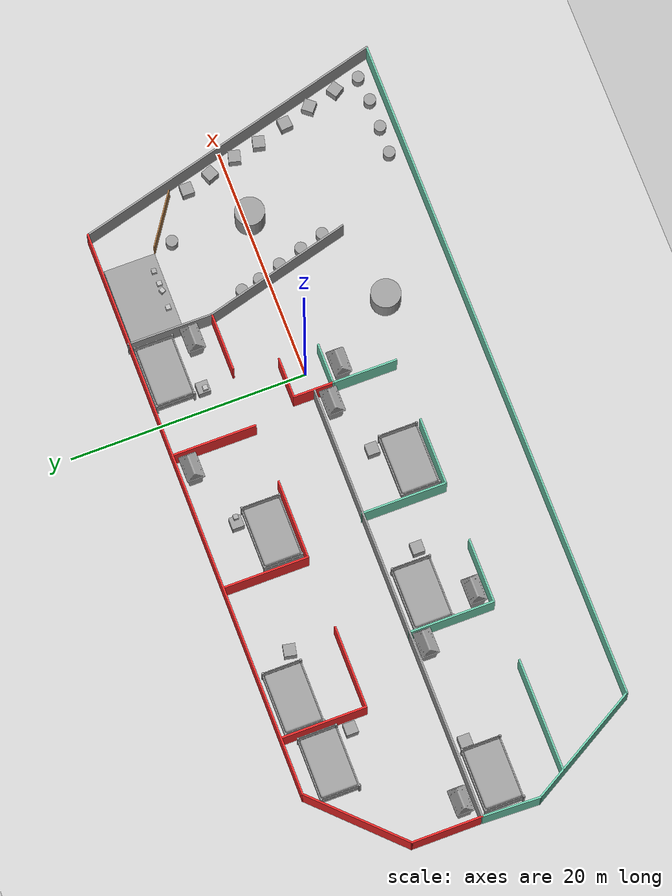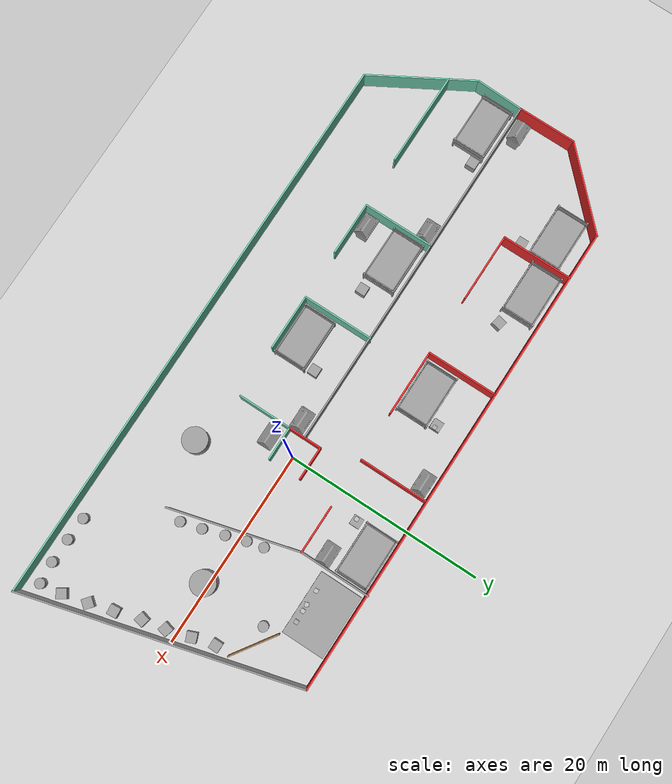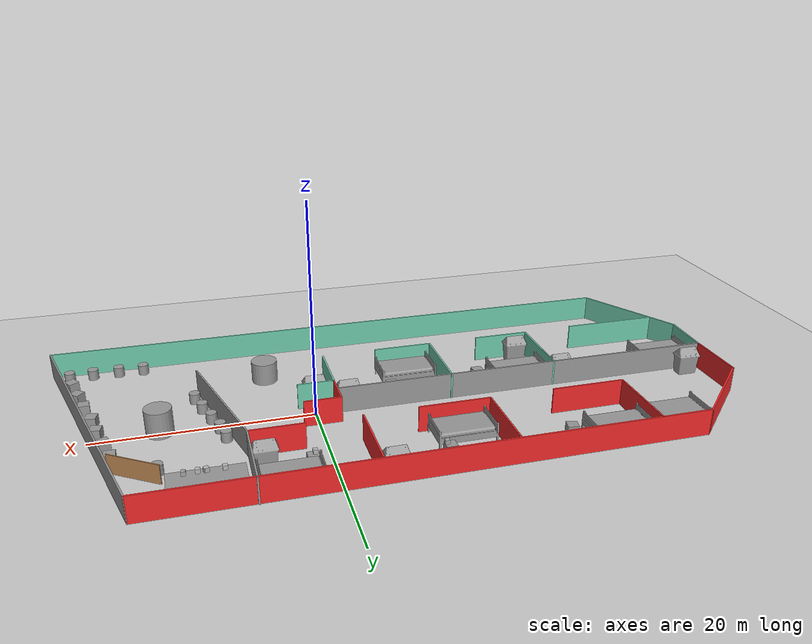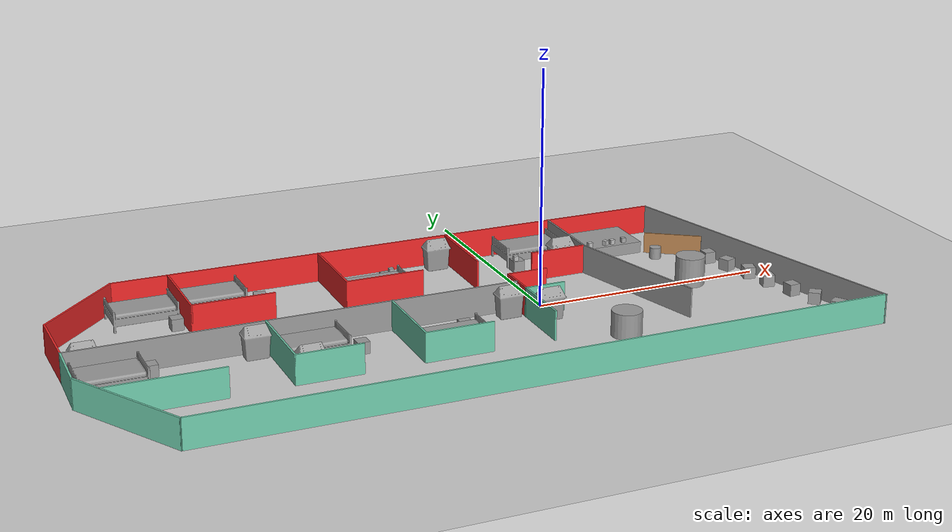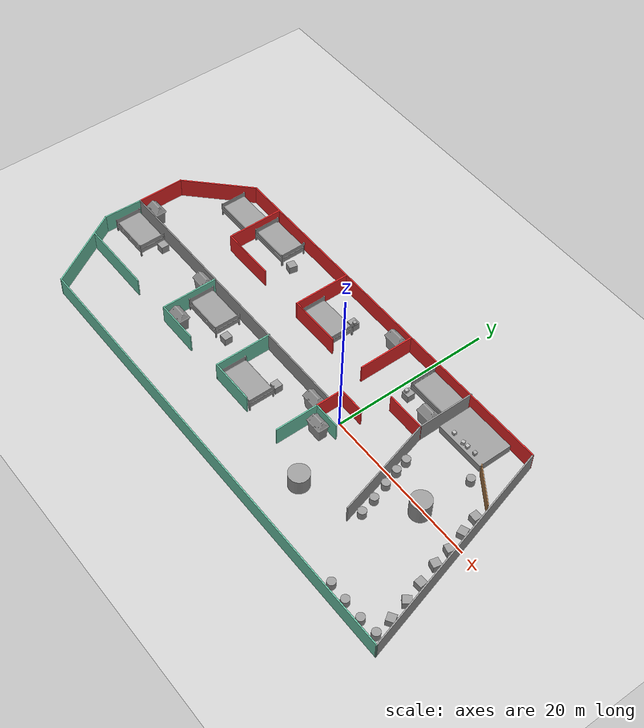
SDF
<sdf version="1.7">
 <world name="default">
  <light name="sun" type="directional">
   <pose>0 0 10 0 -0 0</pose>
   <diffuse>0.8 0.8 0.8 1</diffuse>
   <specular>0.2 0.2 0.2 1</specular>
   <attenuation>
    <range>1000</range>
    <constant>0.9</constant>
    <linear>0.01</linear>
    <quadratic>0.001</quadratic>
   </attenuation>
   <direction>-0.5 0.1 -0.9</direction>
   <spot><inner_angle>0</inner_angle><outer_angle>0</outer_angle><falloff>0</falloff></spot>
  </light>
  <model name="ground_plane">
   <static>1</static>
   <link name="link">
    <collision name="collision">
     <geometry><plane><normal>0 0 1</normal><size>100 100</size></plane></geometry>
     <surface>
      <contact><collide_bitmask>65535</collide_bitmask></contact>
      <friction><ode><mu>100</mu><mu2>50</mu2></ode></friction>
     </surface>
    </collision>
    <visual name="visual">
     <cast_shadows>0</cast_shadows>
     <geometry><plane><normal>0 0 1</normal><size>100 100</size></plane></geometry>
     <material>
      <script><uri>file://media/materials/scripts/gazebo.material</uri><name>Gazebo/Grey</name></script>
     </material>
    </visual>
   </link>
  </model>
  <gravity>0 0 -9.8</gravity>
  <magnetic_field>6e-06 2.3e-05 -4.2e-05</magnetic_field>
  <atmosphere type="adiabatic"/>
  <physics type="ode">
   <max_step_size>0.001</max_step_size>
   <real_time_factor>1</real_time_factor>
   <real_time_update_rate>1000</real_time_update_rate>
  </physics>
  <scene><ambient>0.4 0.4 0.4 1</ambient><background>0.7 0.7 0.7 1</background><shadows>1</shadows></scene>
  <spherical_coordinates>
   <surface_model>EARTH_WGS84</surface_model>
   <latitude_deg>0</latitude_deg>
   <longitude_deg>0</longitude_deg>
   <elevation>0</elevation>
   <heading_deg>0</heading_deg>
  </spherical_coordinates>
  <model name="hospital">
   <pose>-7.85795 -0.812617 0 0 -0 0</pose>
   <link name="Wall_32">
    <collision name="Wall_32_Collision">
     <geometry><box><size>3.5 0.15 2.5</size></box></geometry>
     <pose>0 0 1.25 0 -0 0</pose>
    </collision>
    <visual name="Wall_32_Visual">
     <pose>0 0 1.25 0 -0 0</pose>
     <geometry><box><size>3.5 0.15 2.5</size></box></geometry>
     <material>
      <script><uri>file://media/materials/scripts/gazebo.material</uri><name>Gazebo/Grey</name></script>
      <ambient>0.435294 0.796078 0.67451 1</ambient>
     </material>
     <meta><layer>0</layer></meta>
    </visual>
    <pose>7.48729 -0.777383 0 0 -0 3.14159</pose>
   </link>
   <link name="Wall_33">
    <collision name="Wall_33_Collision">
     <geometry><box><size>3.5 0.15 2.5</size></box></geometry>
     <pose>0 0 1.25 0 -0 0</pose>
    </collision>
    <visual name="Wall_33_Visual">
     <pose>0 0 1.25 0 -0 0</pose>
     <geometry><box><size>3.5 0.15 2.5</size></box></geometry>
     <material>
      <script><uri>file://media/materials/scripts/gazebo.material</uri><name>Gazebo/Grey</name></script>
      <ambient>0.937255 0.160784 0.160784 1</ambient>
     </material>
     <meta><layer>0</layer></meta>
    </visual>
    <pose>5.81229 0.897617 0 0 -0 1.5708</pose>
   </link>
   <link name="Wall_34">
    <collision name="Wall_34_Collision">
     <geometry><box><size>3.5 0.15 2.5</size></box></geometry>
     <pose>0 0 1.25 0 -0 0</pose>
    </collision>
    <visual name="Wall_34_Visual">
     <pose>0 0 1.25 0 -0 0</pose>
     <geometry><box><size>3.5 0.15 2.5</size></box></geometry>
     <material>
      <script><uri>file://media/materials/scripts/gazebo.material</uri><name>Gazebo/Grey</name></script>
      <ambient>0.937255 0.160784 0.160784 1</ambient>
     </material>
     <meta><layer>0</layer></meta>
    </visual>
    <pose>7.48729 2.57262 0 0 -0 0</pose>
   </link>
   <link name="Wall_36">
    <collision name="Wall_36_Collision">
     <geometry><box><size>37.25 0.15 2.5</size></box></geometry>
     <pose>0 0 1.25 0 -0 0</pose>
    </collision>
    <visual name="Wall_36_Visual">
     <pose>0 0 1.25 0 -0 0</pose>
     <geometry><box><size>37.25 0.15 2.5</size></box></geometry>
     <material>
      <script><uri>file://media/materials/scripts/gazebo.material</uri><name>Gazebo/Grey</name></script>
      <ambient>0 0 0 1</ambient>
     </material>
     <meta><layer>0</layer></meta>
    </visual>
    <pose>-12.7871 0.834393 0 0 -0 3.14159</pose>
   </link>
   <link name="Wall_37">
    <collision name="Wall_37_Collision">
     <geometry><box><size>6 0.15 2.5</size></box></geometry>
     <pose>0 0 1.25 0 -0 0</pose>
    </collision>
    <visual name="Wall_37_Visual">
     <pose>0 0 1.25 0 -0 0</pose>
     <geometry><box><size>6 0.15 2.5</size></box></geometry>
     <material>
      <script><uri>file://media/materials/scripts/gazebo.material</uri><name>Gazebo/Grey</name></script>
      <ambient>0.937255 0.160784 0.160784 1</ambient>
     </material>
     <meta><layer>0</layer></meta>
    </visual>
    <pose>-31.3371 3.75939 0 0 -0 1.5708</pose>
   </link>
   <link name="Wall_38">
    <collision name="Wall_38_Collision">
     <geometry><box><size>9.5 0.15 2.5</size></box></geometry>
     <pose>0 0 1.25 0 -0 0</pose>
    </collision>
    <visual name="Wall_38_Visual">
     <pose>0 0 1.25 0 -0 0</pose>
     <geometry><box><size>9.5 0.15 2.5</size></box></geometry>
     <material>
      <script><uri>file://media/materials/scripts/gazebo.material</uri><name>Gazebo/Grey</name></script>
      <ambient>0.937255 0.160784 0.160784 1</ambient>
     </material>
     <meta><layer>0</layer></meta>
    </visual>
    <pose>-28.0313 9.99012 0 0 -0 0.785398</pose>
   </link>
   <link name="Wall_39">
    <collision name="Wall_39_Collision">
     <geometry><box><size>49.25 0.15 2.5</size></box></geometry>
     <pose>0 0 1.25 0 -0 0</pose>
    </collision>
    <visual name="Wall_39_Visual">
     <pose>0 0 1.25 0 -0 0</pose>
     <geometry><box><size>49.25 0.15 2.5</size></box></geometry>
     <material>
      <script><uri>file://media/materials/scripts/gazebo.material</uri><name>Gazebo/Grey</name></script>
      <ambient>0.937255 0.160784 0.160784 1</ambient>
     </material>
     <meta><layer>0</layer></meta>
    </visual>
    <pose>-0.175607 13.2958 0 0 -0 0</pose>
   </link>
   <link name="Wall_40">
    <collision name="Wall_40_Collision">
     <geometry><box><size>27.75 0.15 2.5</size></box></geometry>
     <pose>0 0 1.25 0 -0 0</pose>
    </collision>
    <visual name="Wall_40_Visual">
     <pose>0 0 1.25 0 -0 0</pose>
     <geometry><box><size>27.75 0.15 2.5</size></box></geometry>
     <material>
      <script><uri>file://media/materials/scripts/gazebo.material</uri><name>Gazebo/Grey</name></script>
      <ambient>0 0 0 1</ambient>
     </material>
     <meta><layer>0</layer></meta>
    </visual>
    <pose>27.9461 -0.033935 0 0 -0 -1.309</pose>
   </link>
   <link name="Wall_41">
    <collision name="Wall_41_Collision">
     <geometry><box><size>57.75 0.15 2.5</size></box></geometry>
     <pose>0 0 1.25 0 -0 0</pose>
    </collision>
    <visual name="Wall_41_Visual">
     <pose>0 0 1.25 0 -0 0</pose>
     <geometry><box><size>57.75 0.15 2.5</size></box></geometry>
     <material>
      <script><uri>file://media/materials/scripts/gazebo.material</uri><name>Gazebo/Grey</name></script>
      <ambient>0.435294 0.796078 0.67451 1</ambient>
     </material>
     <meta><layer>0</layer></meta>
    </visual>
    <pose>2.7178 -13.3637 0 0 -0 3.14159</pose>
   </link>
   <link name="Wall_42">
    <collision name="Wall_42_Collision">
     <geometry><box><size>11 0.15 2.5</size></box></geometry>
     <pose>0 0 1.25 0 -0 0</pose>
    </collision>
    <visual name="Wall_42_Visual">
     <pose>0 0 1.25 0 -0 0</pose>
     <geometry><box><size>11 0.15 2.5</size></box></geometry>
     <material>
      <script><uri>file://media/materials/scripts/gazebo.material</uri><name>Gazebo/Grey</name></script>
      <ambient>0.435294 0.796078 0.67451 1</ambient>
     </material>
     <meta><layer>0</layer></meta>
    </visual>
    <pose>-28.7947 -8.66552 0 0 -0 2.0944</pose>
   </link>
   <link name="Wall_43">
    <collision name="Wall_43_Collision">
     <geometry><box><size>4.95474 0.15 2.5</size></box></geometry>
     <pose>0 0 1.25 0 -0 0</pose>
    </collision>
    <visual name="Wall_43_Visual">
     <pose>0 0 1.25 0 -0 0</pose>
     <geometry><box><size>4.95474 0.15 2.5</size></box></geometry>
     <material>
      <script><uri>file://media/materials/scripts/gazebo.material</uri><name>Gazebo/Grey</name></script>
      <ambient>0.435294 0.796078 0.67451 1</ambient>
     </material>
     <meta><layer>0</layer></meta>
    </visual>
    <pose>-31.4221 -1.56647 0 0 -0 1.53538</pose>
   </link>
   <link name="Wall_45">
    <collision name="Wall_45_Collision">
     <geometry><box><size>7.25 0.15 2.5</size></box></geometry>
     <pose>0 0 1.25 0 -0 0</pose>
    </collision>
    <visual name="Wall_45_Visual">
     <pose>0 0 1.25 0 -0 0</pose>
     <geometry><box><size>7.25 0.15 2.5</size></box></geometry>
     <material>
      <script><uri>file://media/materials/scripts/gazebo.material</uri><name>Gazebo/Grey</name></script>
      <ambient>0.435294 0.796078 0.67451 1</ambient>
     </material>
     <meta><layer>0</layer></meta>
    </visual>
    <pose>-15.5179 -2.71252 0 0 -0 -1.5708</pose>
   </link>
   <link name="Wall_48">
    <collision name="Wall_48_Collision">
     <geometry><box><size>5.5 0.15 2.5</size></box></geometry>
     <pose>0 0 1.25 0 -0 0</pose>
    </collision>
    <visual name="Wall_48_Visual">
     <pose>0 0 1.25 0 -0 0</pose>
     <geometry><box><size>5.5 0.15 2.5</size></box></geometry>
     <material>
      <script><uri>file://media/materials/scripts/gazebo.material</uri><name>Gazebo/Grey</name></script>
      <ambient>0.435294 0.796078 0.67451 1</ambient>
     </material>
     <meta><layer>0</layer></meta>
    </visual>
    <pose>5.81229 -3.45238 0 0 -0 -1.5708</pose>
   </link>
   <link name="Wall_50">
    <collision name="Wall_50_Collision">
     <geometry><box><size>7.25 0.15 2.5</size></box></geometry>
     <pose>0 0 1.25 0 -0 0</pose>
    </collision>
    <visual name="Wall_50_Visual">
     <pose>0 0 1.25 0 -0 0</pose>
     <geometry><box><size>7.25 0.15 2.5</size></box></geometry>
     <material>
      <script><uri>file://media/materials/scripts/gazebo.material</uri><name>Gazebo/Grey</name></script>
      <ambient>0.435294 0.796078 0.67451 1</ambient>
     </material>
     <meta><layer>0</layer></meta>
    </visual>
    <pose>-5.11966 -2.65099 0 0 -0 -1.5708</pose>
   </link>
   <link name="Wall_52">
    <collision name="Wall_52_Collision">
     <geometry><box><size>9.5 0.15 2.5</size></box></geometry>
     <pose>0 0 1.25 0 -0 0</pose>
    </collision>
    <visual name="Wall_52_Visual">
     <pose>0 0 1.25 0 -0 0</pose>
     <geometry><box><size>9.5 0.15 2.5</size></box></geometry>
     <material>
      <script><uri>file://media/materials/scripts/gazebo.material</uri><name>Gazebo/Grey</name></script>
      <ambient>0.435294 0.796078 0.67451 1</ambient>
     </material>
     <meta><layer>0</layer></meta>
    </visual>
    <pose>-25.3634 -6.42281 0 0 -0 0</pose>
   </link>
   <link name="Wall_54">
    <collision name="Wall_54_Collision">
     <geometry><box><size>5.5 0.15 2.5</size></box></geometry>
     <pose>0 0 1.25 0 -0 0</pose>
    </collision>
    <visual name="Wall_54_Visual">
     <pose>0 0 1.25 0 -0 0</pose>
     <geometry><box><size>5.5 0.15 2.5</size></box></geometry>
     <material>
      <script><uri>file://media/materials/scripts/gazebo.material</uri><name>Gazebo/Grey</name></script>
      <ambient>0.435294 0.796078 0.67451 1</ambient>
     </material>
     <meta><layer>0</layer></meta>
    </visual>
    <pose>-12.8429 -6.26252 0 0 -0 0</pose>
   </link>
   <link name="Wall_56">
    <collision name="Wall_56_Collision">
     <geometry><box><size>5.75 0.15 2.5</size></box></geometry>
     <pose>0 0 1.25 0 -0 0</pose>
    </collision>
    <visual name="Wall_56_Visual">
     <pose>0 0 1.25 0 -0 0</pose>
     <geometry><box><size>5.75 0.15 2.5</size></box></geometry>
     <material>
      <script><uri>file://media/materials/scripts/gazebo.material</uri><name>Gazebo/Grey</name></script>
      <ambient>0.435294 0.796078 0.67451 1</ambient>
     </material>
     <meta><layer>0</layer></meta>
    </visual>
    <pose>-2.31966 -6.20099 0 0 -0 0</pose>
   </link>
   <link name="Wall_58">
    <collision name="Wall_58_Collision">
     <geometry><box><size>7.25 0.15 2.5</size></box></geometry>
     <pose>0 0 1.25 0 -0 0</pose>
    </collision>
    <visual name="Wall_58_Visual">
     <pose>0 0 1.25 0 -0 0</pose>
     <geometry><box><size>7.25 0.15 2.5</size></box></geometry>
     <material>
      <script><uri>file://media/materials/scripts/gazebo.material</uri><name>Gazebo/Grey</name></script>
      <ambient>0.937255 0.160784 0.160784 1</ambient>
     </material>
     <meta><layer>0</layer></meta>
    </visual>
    <pose>-19.9479 9.71611 0 0 -0 -1.5708</pose>
   </link>
   <link name="Wall_60">
    <collision name="Wall_60_Collision">
     <geometry><box><size>7 0.15 2.5</size></box></geometry>
     <pose>0 0 1.25 0 -0 0</pose>
    </collision>
    <visual name="Wall_60_Visual">
     <pose>0 0 1.25 0 -0 0</pose>
     <geometry><box><size>7 0.15 2.5</size></box></geometry>
     <material>
      <script><uri>file://media/materials/scripts/gazebo.material</uri><name>Gazebo/Grey</name></script>
      <ambient>0.937255 0.160784 0.160784 1</ambient>
     </material>
     <meta><layer>0</layer></meta>
    </visual>
    <pose>-16.5229 6.16611 0 0 -0 0</pose>
   </link>
   <link name="Wall_62">
    <collision name="Wall_62_Collision">
     <geometry><box><size>7.25 0.15 2.5</size></box></geometry>
     <pose>0 0 1.25 0 -0 0</pose>
    </collision>
    <visual name="Wall_62_Visual">
     <pose>0 0 1.25 0 -0 0</pose>
     <geometry><box><size>7.25 0.15 2.5</size></box></geometry>
     <material>
      <script><uri>file://media/materials/scripts/gazebo.material</uri><name>Gazebo/Grey</name></script>
      <ambient>0.937255 0.160784 0.160784 1</ambient>
     </material>
     <meta><layer>0</layer></meta>
    </visual>
    <pose>-6.96549 9.71611 0 0 -0 -1.5708</pose>
   </link>
   <link name="Wall_63">
    <collision name="Wall_63_Collision">
     <geometry><box><size>6.75 0.15 2.5</size></box></geometry>
     <pose>0 0 1.25 0 -0 0</pose>
    </collision>
    <visual name="Wall_63_Visual">
     <pose>0 0 1.25 0 -0 0</pose>
     <geometry><box><size>6.75 0.15 2.5</size></box></geometry>
     <material>
      <script><uri>file://media/materials/scripts/gazebo.material</uri><name>Gazebo/Grey</name></script>
      <ambient>0.937255 0.160784 0.160784 1</ambient>
     </material>
     <meta><layer>0</layer></meta>
    </visual>
    <pose>-3.66549 6.16611 0 0 -0 0</pose>
   </link>
   <link name="Wall_67">
    <collision name="Wall_67_Collision">
     <geometry><box><size>7 0.15 2.5</size></box></geometry>
     <pose>0 0 1.25 0 -0 0</pose>
    </collision>
    <visual name="Wall_67_Visual">
     <pose>0 0 1.25 0 -0 0</pose>
     <geometry><box><size>7 0.15 2.5</size></box></geometry>
     <material>
      <script><uri>file://media/materials/scripts/gazebo.material</uri><name>Gazebo/Grey</name></script>
      <ambient>0.937255 0.160784 0.160784 1</ambient>
     </material>
     <meta><layer>0</layer></meta>
    </visual>
    <pose>4.65913 9.70467 0 0 -0 1.5708</pose>
   </link>
   <link name="Wall_69">
    <collision name="Wall_69_Collision">
     <geometry><box><size>7.25 0.15 2.5</size></box></geometry>
     <pose>0 0 1.25 0 -0 0</pose>
    </collision>
    <visual name="Wall_69_Visual">
     <pose>0 0 1.25 0 -0 0</pose>
     <geometry><box><size>7.25 0.15 2.5</size></box></geometry>
     <material>
      <script><uri>file://media/materials/scripts/gazebo.material</uri><name>Gazebo/Grey</name></script>
      <ambient>0 0 0 1</ambient>
     </material>
     <meta><layer>0</layer></meta>
    </visual>
    <pose>14.5816 9.84116 0 0 -0 -1.5708</pose>
   </link>
   <link name="Wall_70">
    <collision name="Wall_70_Collision">
     <geometry><box><size>5 0.15 2.5</size></box></geometry>
     <pose>0 0 1.25 0 -0 0</pose>
    </collision>
    <visual name="Wall_70_Visual">
     <pose>0 0 1.25 0 -0 0</pose>
     <geometry><box><size>5 0.15 2.5</size></box></geometry>
     <material>
      <script><uri>file://media/materials/scripts/gazebo.material</uri><name>Gazebo/Grey</name></script>
      <ambient>0.937255 0.160784 0.160784 1</ambient>
     </material>
     <meta><layer>0</layer></meta>
    </visual>
    <pose>12.1566 6.29116 0 0 -0 3.14159</pose>
   </link>
   <link name="Wall_72">
    <collision name="Wall_72_Collision">
     <geometry><box><size>13 0.15 2.5</size></box></geometry>
     <pose>0 0 1.25 0 -0 0</pose>
    </collision>
    <visual name="Wall_72_Visual">
     <pose>0 0 1.25 0 -0 0</pose>
     <geometry><box><size>13 0.15 2.5</size></box></geometry>
     <material>
      <script><uri>file://media/materials/scripts/gazebo.material</uri><name>Gazebo/Grey</name></script>
      <ambient>0 0 0 1</ambient>
     </material>
     <meta><layer>0</layer></meta>
    </visual>
    <pose>16.2445 0.085088 0 0 -0 -1.309</pose>
   </link>
   <static>1</static>
  </model>
  <model name="tree">
   <link name="link_12">
    <inertial>
     <mass>1</mass>
     <inertia>
      <ixx>0.166667</ixx>
      <ixy>0</ixy>
      <ixz>0</ixz>
      <iyy>0.166667</iyy>
      <iyz>0</iyz>
      <izz>0.166667</izz>
     </inertia>
    </inertial>
    <pose>2.99776 21.1634 0 0 -0 0</pose>
    <visual name="visual">
     <geometry>
      <mesh><uri>/home/teera/dev_ws/src/tratsah/meshes/dae/trash_can.dae</uri><scale>1 1 1</scale></mesh>
     </geometry>
     <material>
      <lighting>1</lighting>
      <script><uri>file://media/materials/scripts/gazebo.material</uri><name>Gazebo/Grey</name></script>
      <shader type="pixel"/>
     </material>
    </visual>
    <collision name="collision">
     <geometry>
      <mesh><uri>/home/teera/dev_ws/src/tratsah/meshes/dae/trash_can.dae</uri><scale>1 1 1</scale></mesh>
     </geometry>
     <surface>
      <friction>
       <ode><mu>1</mu><mu2>1</mu2><fdir1>0 0 0</fdir1><slip1>0</slip1><slip2>0</slip2></ode>
       <torsional>
        <coefficient>1</coefficient>
        <patch_radius>0</patch_radius>
        <surface_radius>0</surface_radius>
        <use_patch_radius>1</use_patch_radius>
        <ode><slip>0</slip></ode>
       </torsional>
      </friction>
      <bounce><restitution_coefficient>0</restitution_coefficient><threshold>1e+06</threshold></bounce>
      <contact>
       <collide_without_contact>0</collide_without_contact>
       <collide_without_contact_bitmask>1</collide_without_contact_bitmask>
       <collide_bitmask>1</collide_bitmask>
       <ode>
        <soft_cfm>0</soft_cfm>
        <soft_erp>0.2</soft_erp>
        <kp>1e+13</kp>
        <kd>1</kd>
        <max_vel>0.01</max_vel>
        <min_depth>0</min_depth>
       </ode>
       <bullet>
        <split_impulse>1</split_impulse>
        <split_impulse_penetration_threshold>-0.01</split_impulse_penetration_threshold>
        <soft_cfm>0</soft_cfm>
        <soft_erp>0.2</soft_erp>
        <kp>1e+13</kp>
        <kd>1</kd>
       </bullet>
      </contact>
     </surface>
    </collision>
   </link>
   <model name="trash_can">
    <link name="link_12">
     <inertial>
      <mass>1</mass>
      <inertia>
       <ixx>0.166667</ixx>
       <ixy>0</ixy>
       <ixz>0</ixz>
       <iyy>0.166667</iyy>
       <iyz>0</iyz>
       <izz>0.166667</izz>
      </inertia>
     </inertial>
     <pose>4e-06 2.8e-05 0 0 -0 0</pose>
     <visual name="visual">
      <geometry>
       <mesh><uri>/home/teera/dev_ws/src/tratsah/meshes/dae/trash_can.dae</uri><scale>1 1 1</scale></mesh>
      </geometry>
      <material>
       <lighting>1</lighting>
       <script><uri>file://media/materials/scripts/gazebo.material</uri><name>Gazebo/Grey</name></script>
       <shader type="pixel"/>
      </material>
     </visual>
     <collision name="collision">
      <geometry>
       <mesh><uri>/home/teera/dev_ws/src/tratsah/meshes/dae/trash_can.dae</uri><scale>1 1 1</scale></mesh>
      </geometry>
      <surface>
       <friction>
        <ode><mu>1</mu><mu2>1</mu2><fdir1>0 0 0</fdir1><slip1>0</slip1><slip2>0</slip2></ode>
        <torsional>
         <coefficient>1</coefficient>
         <patch_radius>0</patch_radius>
         <surface_radius>0</surface_radius>
         <use_patch_radius>1</use_patch_radius>
         <ode><slip>0</slip></ode>
        </torsional>
       </friction>
       <bounce><restitution_coefficient>0</restitution_coefficient><threshold>1e+06</threshold></bounce>
       <contact>
        <collide_without_contact>0</collide_without_contact>
        <collide_without_contact_bitmask>1</collide_without_contact_bitmask>
        <collide_bitmask>1</collide_bitmask>
        <ode>
         <soft_cfm>0</soft_cfm>
         <soft_erp>0.2</soft_erp>
         <kp>1e+13</kp>
         <kd>1</kd>
         <max_vel>0.01</max_vel>
         <min_depth>0</min_depth>
        </ode>
        <bullet>
         <split_impulse>1</split_impulse>
         <split_impulse_penetration_threshold>-0.01</split_impulse_penetration_threshold>
         <soft_cfm>0</soft_cfm>
         <soft_erp>0.2</soft_erp>
         <kp>1e+13</kp>
         <kd>1</kd>
        </bullet>
       </contact>
      </surface>
     </collision>
    </link>
    <static>0</static>
    <pose>13.0667 17.3666 0 0 -0 0</pose>
   </model>
   <model name="trash_can_0">
    <link name="link_12">
     <inertial>
      <mass>1</mass>
      <inertia>
       <ixx>0.166667</ixx>
       <ixy>0</ixy>
       <ixz>0</ixz>
       <iyy>0.166667</iyy>
       <iyz>0</iyz>
       <izz>0.166667</izz>
      </inertia>
     </inertial>
     <pose>4e-06 2.8e-05 0 0 -0 0</pose>
     <visual name="visual">
      <geometry>
       <mesh><uri>/home/teera/dev_ws/src/tratsah/meshes/dae/trash_can.dae</uri><scale>1 1 1</scale></mesh>
      </geometry>
      <material>
       <lighting>1</lighting>
       <script><uri>file://media/materials/scripts/gazebo.material</uri><name>Gazebo/Grey</name></script>
       <shader type="pixel"/>
      </material>
     </visual>
     <collision name="collision">
      <geometry>
       <mesh><uri>/home/teera/dev_ws/src/tratsah/meshes/dae/trash_can.dae</uri><scale>1 1 1</scale></mesh>
      </geometry>
      <surface>
       <friction>
        <ode><mu>1</mu><mu2>1</mu2><fdir1>0 0 0</fdir1><slip1>0</slip1><slip2>0</slip2></ode>
        <torsional>
         <coefficient>1</coefficient>
         <patch_radius>0</patch_radius>
         <surface_radius>0</surface_radius>
         <use_patch_radius>1</use_patch_radius>
         <ode><slip>0</slip></ode>
        </torsional>
       </friction>
       <bounce><restitution_coefficient>0</restitution_coefficient><threshold>1e+06</threshold></bounce>
       <contact>
        <collide_without_contact>0</collide_without_contact>
        <collide_without_contact_bitmask>1</collide_without_contact_bitmask>
        <collide_bitmask>1</collide_bitmask>
        <ode>
         <soft_cfm>0</soft_cfm>
         <soft_erp>0.2</soft_erp>
         <kp>1e+13</kp>
         <kd>1</kd>
         <max_vel>0.01</max_vel>
         <min_depth>0</min_depth>
        </ode>
        <bullet>
         <split_impulse>1</split_impulse>
         <split_impulse_penetration_threshold>-0.01</split_impulse_penetration_threshold>
         <soft_cfm>0</soft_cfm>
         <soft_erp>0.2</soft_erp>
         <kp>1e+13</kp>
         <kd>1</kd>
        </bullet>
       </contact>
      </surface>
     </collision>
    </link>
    <static>0</static>
    <pose>-14.3091 3.77436 0 0 -0 0</pose>
   </model>
   <model name="trash_can_1">
    <link name="link_12">
     <inertial>
      <mass>1</mass>
      <inertia>
       <ixx>0.166667</ixx>
       <ixy>0</ixy>
       <ixz>0</ixz>
       <iyy>0.166667</iyy>
       <iyz>0</iyz>
       <izz>0.166667</izz>
      </inertia>
     </inertial>
     <pose>4e-06 2.8e-05 0 0 -0 0</pose>
     <visual name="visual">
      <geometry>
       <mesh><uri>/home/teera/dev_ws/src/tratsah/meshes/dae/trash_can.dae</uri><scale>1 1 1</scale></mesh>
      </geometry>
      <material>
       <lighting>1</lighting>
       <script><uri>file://media/materials/scripts/gazebo.material</uri><name>Gazebo/Grey</name></script>
       <shader type="pixel"/>
      </material>
     </visual>
     <collision name="collision">
      <geometry>
       <mesh><uri>/home/teera/dev_ws/src/tratsah/meshes/dae/trash_can.dae</uri><scale>1 1 1</scale></mesh>
      </geometry>
      <surface>
       <friction>
        <ode><mu>1</mu><mu2>1</mu2><fdir1>0 0 0</fdir1><slip1>0</slip1><slip2>0</slip2></ode>
        <torsional>
         <coefficient>1</coefficient>
         <patch_radius>0</patch_radius>
         <surface_radius>0</surface_radius>
         <use_patch_radius>1</use_patch_radius>
         <ode><slip>0</slip></ode>
        </torsional>
       </friction>
       <bounce><restitution_coefficient>0</restitution_coefficient><threshold>1e+06</threshold></bounce>
       <contact>
        <collide_without_contact>0</collide_without_contact>
        <collide_without_contact_bitmask>1</collide_without_contact_bitmask>
        <collide_bitmask>1</collide_bitmask>
        <ode>
         <soft_cfm>0</soft_cfm>
         <soft_erp>0.2</soft_erp>
         <kp>1e+13</kp>
         <kd>1</kd>
         <max_vel>0.01</max_vel>
         <min_depth>0</min_depth>
        </ode>
        <bullet>
         <split_impulse>1</split_impulse>
         <split_impulse_penetration_threshold>-0.01</split_impulse_penetration_threshold>
         <soft_cfm>0</soft_cfm>
         <soft_erp>0.2</soft_erp>
         <kp>1e+13</kp>
         <kd>1</kd>
        </bullet>
       </contact>
      </surface>
     </collision>
    </link>
    <static>0</static>
    <pose>7.06906 7.11266 0 0 -0 0</pose>
   </model>
   <model name="trash_can_2">
    <link name="link_12">
     <inertial>
      <mass>1</mass>
      <inertia>
       <ixx>0.166667</ixx>
       <ixy>0</ixy>
       <ixz>0</ixz>
       <iyy>0.166667</iyy>
       <iyz>0</iyz>
       <izz>0.166667</izz>
      </inertia>
     </inertial>
     <pose>4e-06 2.8e-05 0 0 -0 0</pose>
     <visual name="visual">
      <geometry>
       <mesh><uri>/home/teera/dev_ws/src/tratsah/meshes/dae/trash_can.dae</uri><scale>1 1 1</scale></mesh>
      </geometry>
      <material>
       <lighting>1</lighting>
       <script><uri>file://media/materials/scripts/gazebo.material</uri><name>Gazebo/Grey</name></script>
       <shader type="pixel"/>
      </material>
     </visual>
     <collision name="collision">
      <geometry>
       <mesh><uri>/home/teera/dev_ws/src/tratsah/meshes/dae/trash_can.dae</uri><scale>1 1 1</scale></mesh>
      </geometry>
      <surface>
       <friction>
        <ode><mu>1</mu><mu2>1</mu2><fdir1>0 0 0</fdir1><slip1>0</slip1><slip2>0</slip2></ode>
        <torsional>
         <coefficient>1</coefficient>
         <patch_radius>0</patch_radius>
         <surface_radius>0</surface_radius>
         <use_patch_radius>1</use_patch_radius>
         <ode><slip>0</slip></ode>
        </torsional>
       </friction>
       <bounce><restitution_coefficient>0</restitution_coefficient><threshold>1e+06</threshold></bounce>
       <contact>
        <collide_without_contact>0</collide_without_contact>
        <collide_without_contact_bitmask>1</collide_without_contact_bitmask>
        <collide_bitmask>1</collide_bitmask>
        <ode>
         <soft_cfm>0</soft_cfm>
         <soft_erp>0.2</soft_erp>
         <kp>1e+13</kp>
         <kd>1</kd>
         <max_vel>0.01</max_vel>
         <min_depth>0</min_depth>
        </ode>
        <bullet>
         <split_impulse>1</split_impulse>
         <split_impulse_penetration_threshold>-0.01</split_impulse_penetration_threshold>
         <soft_cfm>0</soft_cfm>
         <soft_erp>0.2</soft_erp>
         <kp>1e+13</kp>
         <kd>1</kd>
        </bullet>
       </contact>
      </surface>
     </collision>
    </link>
    <static>0</static>
    <pose>-17.0093 8.86572 0 0 -0 0</pose>
   </model>
   <model name="trash_can_3">
    <link name="link_12">
     <inertial>
      <mass>1</mass>
      <inertia>
       <ixx>0.166667</ixx>
       <ixy>0</ixy>
       <ixz>0</ixz>
       <iyy>0.166667</iyy>
       <iyz>0</iyz>
       <izz>0.166667</izz>
      </inertia>
     </inertial>
     <pose>4e-06 2.8e-05 0 0 -0 0</pose>
     <visual name="visual">
      <geometry>
       <mesh><uri>/home/teera/dev_ws/src/tratsah/meshes/dae/trash_can.dae</uri><scale>1 1 1</scale></mesh>
      </geometry>
      <material>
       <lighting>1</lighting>
       <script><uri>file://media/materials/scripts/gazebo.material</uri><name>Gazebo/Grey</name></script>
       <shader type="pixel"/>
      </material>
     </visual>
     <collision name="collision">
      <geometry>
       <mesh><uri>/home/teera/dev_ws/src/tratsah/meshes/dae/trash_can.dae</uri><scale>1 1 1</scale></mesh>
      </geometry>
      <surface>
       <friction>
        <ode><mu>1</mu><mu2>1</mu2><fdir1>0 0 0</fdir1><slip1>0</slip1><slip2>0</slip2></ode>
        <torsional>
         <coefficient>1</coefficient>
         <patch_radius>0</patch_radius>
         <surface_radius>0</surface_radius>
         <use_patch_radius>1</use_patch_radius>
         <ode><slip>0</slip></ode>
        </torsional>
       </friction>
       <bounce><restitution_coefficient>0</restitution_coefficient><threshold>1e+06</threshold></bounce>
       <contact>
        <collide_without_contact>0</collide_without_contact>
        <collide_without_contact_bitmask>1</collide_without_contact_bitmask>
        <collide_bitmask>1</collide_bitmask>
        <ode>
         <soft_cfm>0</soft_cfm>
         <soft_erp>0.2</soft_erp>
         <kp>1e+13</kp>
         <kd>1</kd>
         <max_vel>0.01</max_vel>
         <min_depth>0</min_depth>
        </ode>
        <bullet>
         <split_impulse>1</split_impulse>
         <split_impulse_penetration_threshold>-0.01</split_impulse_penetration_threshold>
         <soft_cfm>0</soft_cfm>
         <soft_erp>0.2</soft_erp>
         <kp>1e+13</kp>
         <kd>1</kd>
        </bullet>
       </contact>
      </surface>
     </collision>
    </link>
    <static>0</static>
    <pose>4.20413 8.77388 0 0 -0 0</pose>
   </model>
   <model name="trash_can_4">
    <link name="link_12">
     <inertial>
      <mass>1</mass>
      <inertia>
       <ixx>0.166667</ixx>
       <ixy>0</ixy>
       <ixz>0</ixz>
       <iyy>0.166667</iyy>
       <iyz>0</iyz>
       <izz>0.166667</izz>
      </inertia>
     </inertial>
     <pose>4e-06 2.8e-05 0 0 -0 0</pose>
     <visual name="visual">
      <geometry>
       <mesh><uri>/home/teera/dev_ws/src/tratsah/meshes/dae/trash_can.dae</uri><scale>1 1 1</scale></mesh>
      </geometry>
      <material>
       <lighting>1</lighting>
       <script><uri>file://media/materials/scripts/gazebo.material</uri><name>Gazebo/Grey</name></script>
       <shader type="pixel"/>
      </material>
     </visual>
     <collision name="collision">
      <geometry>
       <mesh><uri>/home/teera/dev_ws/src/tratsah/meshes/dae/trash_can.dae</uri><scale>1 1 1</scale></mesh>
      </geometry>
      <surface>
       <friction>
        <ode><mu>1</mu><mu2>1</mu2><fdir1>0 0 0</fdir1><slip1>0</slip1><slip2>0</slip2></ode>
        <torsional>
         <coefficient>1</coefficient>
         <patch_radius>0</patch_radius>
         <surface_radius>0</surface_radius>
         <use_patch_radius>1</use_patch_radius>
         <ode><slip>0</slip></ode>
        </torsional>
       </friction>
       <bounce><restitution_coefficient>0</restitution_coefficient><threshold>1e+06</threshold></bounce>
       <contact>
        <collide_without_contact>0</collide_without_contact>
        <collide_without_contact_bitmask>1</collide_without_contact_bitmask>
        <collide_bitmask>1</collide_bitmask>
        <ode>
         <soft_cfm>0</soft_cfm>
         <soft_erp>0.2</soft_erp>
         <kp>1e+13</kp>
         <kd>1</kd>
         <max_vel>0.01</max_vel>
         <min_depth>0</min_depth>
        </ode>
        <bullet>
         <split_impulse>1</split_impulse>
         <split_impulse_penetration_threshold>-0.01</split_impulse_penetration_threshold>
         <soft_cfm>0</soft_cfm>
         <soft_erp>0.2</soft_erp>
         <kp>1e+13</kp>
         <kd>1</kd>
        </bullet>
       </contact>
      </surface>
     </collision>
    </link>
    <static>0</static>
    <pose>-29.8163 10.8728 0 0 -0 0</pose>
   </model>
   <static>0</static>
   <pose>-7.52959 -9.8007 0.007877 -0 -0 -0</pose>
  </model>
  <model name="blue_box">
   <model name="blue_box">
    <link name="new_link">
     <visual name="top_visual">
      <geometry><mesh><uri>model://blue_box/meshes/blue_box.dae</uri></mesh></geometry>
     </visual>
     <collision name="collision">
      <geometry><box><size>0.4 0.4 0.4</size></box></geometry>
      <origin xyz="0 0 0" rpy="0 0 0"/>
     </collision>
     <inertial>
      <mass>1</mass>
      <inertia><ixx>0.01</ixx><ixy>0</ixy><ixz>0</ixz><iyy>0.01</iyy><iyz>0</iyz><izz>0.01</izz></inertia>
     </inertial>
    </link>
   </model>
   <static>0</static>
   <pose>1.50463 8.00874 1.2 -3.4e-05 1.2e-05 -0.029</pose>
  </model>
  <model name="red_box">
   <model name="green_box">
    <link name="new_link">
     <visual name="top_visual">
      <geometry><mesh><uri>model://red_box/meshes/red_box.dae</uri></mesh></geometry>
     </visual>
     <collision name="collision">
      <geometry><box><size>0.4 0.4 0.4</size></box></geometry>
      <origin xyz="0 0 0" rpy="0 0 0"/>
     </collision>
     <inertial>
      <mass>1</mass>
      <inertia><ixx>0.01</ixx><ixy>0</ixy><ixz>0</ixz><iyy>0.01</iyy><iyz>0</iyz><izz>0.01</izz></inertia>
     </inertial>
    </link>
    <pose>-2e-06 -0 -0 0 -0 0</pose>
   </model>
   <static>0</static>
   <pose>-9.41712 9.46674 1.2 -1e-06 1e-06 -0.002889</pose>
  </model>
  <model name="blue_box_0">
   <link name="new_link">
    <visual name="top_visual">
     <geometry><mesh><uri>model://blue_box/meshes/blue_box.dae</uri></mesh></geometry>
    </visual>
    <collision name="collision">
     <geometry><box><size>0.4 0.4 0.4</size></box></geometry>
     <origin xyz="0 0 0" rpy="0 0 0"/>
    </collision>
    <inertial>
     <mass>1</mass>
     <inertia><ixx>0.01</ixx><ixy>0</ixy><ixz>0</ixz><iyy>0.01</iyy><iyz>0</iyz><izz>0.01</izz></inertia>
    </inertial>
   </link>
   <pose>8.87755 8.46569 1.2 2.1e-05 -0 0.023989</pose>
  </model>
  <model name="green_box_0">
   <link name="new_link">
    <visual name="top_visual">
     <geometry><mesh><uri>model://green_box/meshes/green_box.dae</uri><scale>1 1 1</scale></mesh></geometry>
    </visual>
    <collision name="collision">
     <geometry><box><size>0.4 0.4 0.4</size></box></geometry>
     <origin xyz="0 0 0" rpy="0 0 0"/>
    </collision>
    <inertial>
     <mass>1</mass>
     <inertia><ixx>0.01</ixx><ixy>0</ixy><ixz>0</ixz><iyy>0.01</iyy><iyz>0</iyz><izz>0.01</izz></inertia>
    </inertial>
   </link>
   <pose>10.3679 8.41236 1.2 2.1e-05 -0 0.409241</pose>
  </model>
  <model name="green_box_1">
   <link name="new_link">
    <visual name="top_visual">
     <geometry><mesh><uri>model://red_box/meshes/red_box.dae</uri></mesh></geometry>
    </visual>
    <collision name="collision">
     <geometry><box><size>0.4 0.4 0.4</size></box></geometry>
     <origin xyz="0 0 0" rpy="0 0 0"/>
    </collision>
    <inertial>
     <mass>1</mass>
     <inertia><ixx>0.01</ixx><ixy>0</ixy><ixz>0</ixz><iyy>0.01</iyy><iyz>0</iyz><izz>0.01</izz></inertia>
    </inertial>
   </link>
   <pose>12.1566 8.47956 1.19999 0 2.4e-05 -0.042184</pose>
  </model>
  <model name="blue_box_1">
   <link name="new_link">
    <visual name="top_visual">
     <geometry><mesh><uri>model://blue_box/meshes/blue_box.dae</uri></mesh></geometry>
    </visual>
    <collision name="collision">
     <geometry><box><size>0.4 0.4 0.4</size></box></geometry>
     <origin xyz="0 0 0" rpy="0 0 0"/>
    </collision>
    <inertial>
     <mass>1</mass>
     <inertia><ixx>0.01</ixx><ixy>0</ixy><ixz>0</ixz><iyy>0.01</iyy><iyz>0</iyz><izz>0.01</izz></inertia>
    </inertial>
   </link>
   <pose>11.0299 8.42962 1.2 2.2e-05 0 -0.021269</pose>
  </model>
  <model name="unit_box_1">
   <link name="link">
    <inertial>
     <mass>100</mass>
     <inertia><ixx>164.686</ixx><ixy>0</ixy><ixz>0</ixz><iyy>354.534</iyy><iyz>0</iyz><izz>502.553</izz></inertia>
    </inertial>
    <visual name="visual">
     <geometry><box><size>6.44547 4.33155 1</size></box></geometry>
     <material>
      <script><name>Gazebo/Grey</name><uri>file://media/materials/scripts/gazebo.material</uri></script>
      <shader type="pixel"><normal_map>__default__</normal_map></shader>
     </material>
    </visual>
    <collision name="collision">
     <geometry><box><size>6.44547 4.33155 1</size></box></geometry>
     <surface>
      <friction>
       <ode><mu>1</mu><mu2>1</mu2><fdir1>0 0 0</fdir1><slip1>0</slip1><slip2>0</slip2></ode>
       <torsional>
        <coefficient>1</coefficient>
        <patch_radius>0</patch_radius>
        <surface_radius>0</surface_radius>
        <use_patch_radius>1</use_patch_radius>
        <ode><slip>0</slip></ode>
       </torsional>
      </friction>
      <bounce><restitution_coefficient>0</restitution_coefficient><threshold>1e+06</threshold></bounce>
      <contact>
       <collide_without_contact>0</collide_without_contact>
       <collide_without_contact_bitmask>1</collide_without_contact_bitmask>
       <collide_bitmask>1</collide_bitmask>
       <ode>
        <soft_cfm>0</soft_cfm>
        <soft_erp>0.2</soft_erp>
        <kp>1e+13</kp>
        <kd>1</kd>
        <max_vel>0.01</max_vel>
        <min_depth>0</min_depth>
       </ode>
       <bullet>
        <split_impulse>1</split_impulse>
        <split_impulse_penetration_threshold>-0.01</split_impulse_penetration_threshold>
        <soft_cfm>0</soft_cfm>
        <soft_erp>0.2</soft_erp>
        <kp>1e+13</kp>
        <kd>1</kd>
       </bullet>
      </contact>
     </surface>
    </collision>
   </link>
   <static>0</static>
   <pose>10.3977 10.0716 0.5 0 -0 3e-06</pose>
  </model>
  <model name="unit_box">
   <link name="link">
    <inertial>
     <mass>50</mass>
     <inertia><ixx>8.33333</ixx><ixy>0</ixy><ixz>0</ixz><iyy>8.33333</iyy><iyz>0</iyz><izz>8.33333</izz></inertia>
    </inertial>
    <visual name="visual">
     <geometry><box><size>1 1 1</size></box></geometry>
     <material>
      <script><name>Gazebo/Grey</name><uri>file://media/materials/scripts/gazebo.material</uri></script>
      <shader type="pixel"><normal_map>__default__</normal_map></shader>
     </material>
    </visual>
    <collision name="collision">
     <geometry><box><size>1 1 1</size></box></geometry>
     <surface>
      <friction>
       <ode><mu>1</mu><mu2>1</mu2><fdir1>0 0 0</fdir1><slip1>0</slip1><slip2>0</slip2></ode>
       <torsional>
        <coefficient>1</coefficient>
        <patch_radius>0</patch_radius>
        <surface_radius>0</surface_radius>
        <use_patch_radius>1</use_patch_radius>
        <ode><slip>0</slip></ode>
       </torsional>
      </friction>
      <bounce><restitution_coefficient>0</restitution_coefficient><threshold>1e+06</threshold></bounce>
      <contact>
       <collide_without_contact>0</collide_without_contact>
       <collide_without_contact_bitmask>1</collide_without_contact_bitmask>
       <collide_bitmask>1</collide_bitmask>
       <ode>
        <soft_cfm>0</soft_cfm>
        <soft_erp>0.2</soft_erp>
        <kp>1e+13</kp>
        <kd>1</kd>
        <max_vel>0.01</max_vel>
        <min_depth>0</min_depth>
       </ode>
       <bullet>
        <split_impulse>1</split_impulse>
        <split_impulse_penetration_threshold>-0.01</split_impulse_penetration_threshold>
        <soft_cfm>0</soft_cfm>
        <soft_erp>0.2</soft_erp>
        <kp>1e+13</kp>
        <kd>1</kd>
       </bullet>
      </contact>
     </surface>
    </collision>
   </link>
   <static>0</static>
   <pose>1.69663 8.14969 0.5 0 0 -7e-06</pose>
  </model>
  <model name="unit_box_0">
   <link name="link">
    <inertial>
     <mass>50</mass>
     <inertia><ixx>8.33333</ixx><ixy>0</ixy><ixz>0</ixz><iyy>8.33333</iyy><iyz>0</iyz><izz>8.33333</izz></inertia>
    </inertial>
    <visual name="visual">
     <geometry><box><size>1 1 1</size></box></geometry>
     <material>
      <script><name>Gazebo/Grey</name><uri>file://media/materials/scripts/gazebo.material</uri></script>
      <shader type="pixel"><normal_map>__default__</normal_map></shader>
     </material>
    </visual>
    <collision name="collision">
     <geometry><box><size>1 1 1</size></box></geometry>
     <surface>
      <friction>
       <ode><mu>1</mu><mu2>1</mu2><fdir1>0 0 0</fdir1><slip1>0</slip1><slip2>0</slip2></ode>
       <torsional>
        <coefficient>1</coefficient>
        <patch_radius>0</patch_radius>
        <surface_radius>0</surface_radius>
        <use_patch_radius>1</use_patch_radius>
        <ode><slip>0</slip></ode>
       </torsional>
      </friction>
      <bounce><restitution_coefficient>0</restitution_coefficient><threshold>1e+06</threshold></bounce>
      <contact>
       <collide_without_contact>0</collide_without_contact>
       <collide_without_contact_bitmask>1</collide_without_contact_bitmask>
       <collide_bitmask>1</collide_bitmask>
       <ode>
        <soft_cfm>0</soft_cfm>
        <soft_erp>0.2</soft_erp>
        <kp>1e+13</kp>
        <kd>1</kd>
        <max_vel>0.01</max_vel>
        <min_depth>0</min_depth>
       </ode>
       <bullet>
        <split_impulse>1</split_impulse>
        <split_impulse_penetration_threshold>-0.01</split_impulse_penetration_threshold>
        <soft_cfm>0</soft_cfm>
        <soft_erp>0.2</soft_erp>
        <kp>1e+13</kp>
        <kd>1</kd>
       </bullet>
      </contact>
     </surface>
    </collision>
   </link>
   <static>0</static>
   <pose>-9.74899 9.53266 0.5 -1e-06 1e-06 -0.000148</pose>
  </model>
  <model name="unit_box_2">
   <link name="link">
    <inertial>
     <mass>50</mass>
     <inertia><ixx>8.33333</ixx><ixy>0</ixy><ixz>0</ixz><iyy>8.33333</iyy><iyz>0</iyz><izz>8.33333</izz></inertia>
    </inertial>
    <visual name="visual">
     <geometry><box><size>1 1 1</size></box></geometry>
     <material>
      <script><name>Gazebo/Grey</name><uri>file://media/materials/scripts/gazebo.material</uri></script>
      <shader type="pixel"><normal_map>__default__</normal_map></shader>
     </material>
    </visual>
    <collision name="collision">
     <geometry><box><size>1 1 1</size></box></geometry>
     <surface>
      <friction>
       <ode><mu>1</mu><mu2>1</mu2><fdir1>0 0 0</fdir1><slip1>0</slip1><slip2>0</slip2></ode>
       <torsional>
        <coefficient>1</coefficient>
        <patch_radius>0</patch_radius>
        <surface_radius>0</surface_radius>
        <use_patch_radius>1</use_patch_radius>
        <ode><slip>0</slip></ode>
       </torsional>
      </friction>
      <bounce><restitution_coefficient>0</restitution_coefficient><threshold>1e+06</threshold></bounce>
      <contact>
       <collide_without_contact>0</collide_without_contact>
       <collide_without_contact_bitmask>1</collide_without_contact_bitmask>
       <collide_bitmask>1</collide_bitmask>
       <ode>
        <soft_cfm>0</soft_cfm>
        <soft_erp>0.2</soft_erp>
        <kp>1e+13</kp>
        <kd>1</kd>
        <max_vel>0.01</max_vel>
        <min_depth>0</min_depth>
       </ode>
       <bullet>
        <split_impulse>1</split_impulse>
        <split_impulse_penetration_threshold>-0.01</split_impulse_penetration_threshold>
        <soft_cfm>0</soft_cfm>
        <soft_erp>0.2</soft_erp>
        <kp>1e+13</kp>
        <kd>1</kd>
       </bullet>
      </contact>
     </surface>
    </collision>
   </link>
   <static>0</static>
   <pose>-7.85792 -2.71407 0.5 0 -0 0</pose>
  </model>
  <model name="unit_box_3">
   <link name="link">
    <inertial>
     <mass>50</mass>
     <inertia><ixx>8.33333</ixx><ixy>0</ixy><ixz>0</ixz><iyy>8.33333</iyy><iyz>0</iyz><izz>8.33333</izz></inertia>
    </inertial>
    <visual name="visual">
     <geometry><box><size>1 1 1</size></box></geometry>
     <material>
      <script><name>Gazebo/Grey</name><uri>file://media/materials/scripts/gazebo.material</uri></script>
      <shader type="pixel"><normal_map>__default__</normal_map></shader>
     </material>
    </visual>
    <collision name="collision">
     <geometry><box><size>1 1 1</size></box></geometry>
     <surface>
      <friction>
       <ode><mu>1</mu><mu2>1</mu2><fdir1>0 0 0</fdir1><slip1>0</slip1><slip2>0</slip2></ode>
       <torsional>
        <coefficient>1</coefficient>
        <patch_radius>0</patch_radius>
        <surface_radius>0</surface_radius>
        <use_patch_radius>1</use_patch_radius>
        <ode><slip>0</slip></ode>
       </torsional>
      </friction>
      <bounce><restitution_coefficient>0</restitution_coefficient><threshold>1e+06</threshold></bounce>
      <contact>
       <collide_without_contact>0</collide_without_contact>
       <collide_without_contact_bitmask>1</collide_without_contact_bitmask>
       <collide_bitmask>1</collide_bitmask>
       <ode>
        <soft_cfm>0</soft_cfm>
        <soft_erp>0.2</soft_erp>
        <kp>1e+13</kp>
        <kd>1</kd>
        <max_vel>0.01</max_vel>
        <min_depth>0</min_depth>
       </ode>
       <bullet>
        <split_impulse>1</split_impulse>
        <split_impulse_penetration_threshold>-0.01</split_impulse_penetration_threshold>
        <soft_cfm>0</soft_cfm>
        <soft_erp>0.2</soft_erp>
        <kp>1e+13</kp>
        <kd>1</kd>
       </bullet>
      </contact>
     </surface>
    </collision>
   </link>
   <static>0</static>
   <pose>-16.7473 -3.16546 0.5 0 -0 0</pose>
  </model>
  <model name="unit_box_4">
   <link name="link">
    <inertial>
     <mass>50</mass>
     <inertia><ixx>8.33333</ixx><ixy>0</ixy><ixz>0</ixz><iyy>8.33333</iyy><iyz>0</iyz><izz>8.33333</izz></inertia>
    </inertial>
    <visual name="visual">
     <geometry><box><size>1 1 1</size></box></geometry>
     <material>
      <script><name>Gazebo/Grey</name><uri>file://media/materials/scripts/gazebo.material</uri></script>
      <shader type="pixel"><normal_map>__default__</normal_map></shader>
     </material>
    </visual>
    <collision name="collision">
     <geometry><box><size>1 1 1</size></box></geometry>
     <surface>
      <friction>
       <ode><mu>1</mu><mu2>1</mu2><fdir1>0 0 0</fdir1><slip1>0</slip1><slip2>0</slip2></ode>
       <torsional>
        <coefficient>1</coefficient>
        <patch_radius>0</patch_radius>
        <surface_radius>0</surface_radius>
        <use_patch_radius>1</use_patch_radius>
        <ode><slip>0</slip></ode>
       </torsional>
      </friction>
      <bounce><restitution_coefficient>0</restitution_coefficient><threshold>1e+06</threshold></bounce>
      <contact>
       <collide_without_contact>0</collide_without_contact>
       <collide_without_contact_bitmask>1</collide_without_contact_bitmask>
       <collide_bitmask>1</collide_bitmask>
       <ode>
        <soft_cfm>0</soft_cfm>
        <soft_erp>0.2</soft_erp>
        <kp>1e+13</kp>
        <kd>1</kd>
        <max_vel>0.01</max_vel>
        <min_depth>0</min_depth>
       </ode>
       <bullet>
        <split_impulse>1</split_impulse>
        <split_impulse_penetration_threshold>-0.01</split_impulse_penetration_threshold>
        <soft_cfm>0</soft_cfm>
        <soft_erp>0.2</soft_erp>
        <kp>1e+13</kp>
        <kd>1</kd>
       </bullet>
      </contact>
     </surface>
    </collision>
   </link>
   <static>0</static>
   <pose>-21.0387 9.24892 0.5 0 0 -0.202587</pose>
  </model>
  <model name="unit_box_5">
   <link name="link">
    <inertial>
     <mass>50</mass>
     <inertia><ixx>8.33333</ixx><ixy>0</ixy><ixz>0</ixz><iyy>8.33333</iyy><iyz>0</iyz><izz>8.33333</izz></inertia>
    </inertial>
    <visual name="visual">
     <geometry><box><size>1 1 1</size></box></geometry>
     <material>
      <script><name>Gazebo/Grey</name><uri>file://media/materials/scripts/gazebo.material</uri></script>
      <shader type="pixel"><normal_map>__default__</normal_map></shader>
     </material>
    </visual>
    <collision name="collision">
     <geometry><box><size>1 1 1</size></box></geometry>
     <surface>
      <friction>
       <ode><mu>1</mu><mu2>1</mu2><fdir1>0 0 0</fdir1><slip1>0</slip1><slip2>0</slip2></ode>
       <torsional>
        <coefficient>1</coefficient>
        <patch_radius>0</patch_radius>
        <surface_radius>0</surface_radius>
        <use_patch_radius>1</use_patch_radius>
        <ode><slip>0</slip></ode>
       </torsional>
      </friction>
      <bounce><restitution_coefficient>0</restitution_coefficient><threshold>1e+06</threshold></bounce>
      <contact>
       <collide_without_contact>0</collide_without_contact>
       <collide_without_contact_bitmask>1</collide_without_contact_bitmask>
       <collide_bitmask>1</collide_bitmask>
       <ode>
        <soft_cfm>0</soft_cfm>
        <soft_erp>0.2</soft_erp>
        <kp>1e+13</kp>
        <kd>1</kd>
        <max_vel>0.01</max_vel>
        <min_depth>0</min_depth>
       </ode>
       <bullet>
        <split_impulse>1</split_impulse>
        <split_impulse_penetration_threshold>-0.01</split_impulse_penetration_threshold>
        <soft_cfm>0</soft_cfm>
        <soft_erp>0.2</soft_erp>
        <kp>1e+13</kp>
        <kd>1</kd>
       </bullet>
      </contact>
     </surface>
    </collision>
   </link>
   <static>0</static>
   <pose>-28.6471 6.9794 0.5 0 -0 0</pose>
  </model>
  <model name="unit_box_6">
   <link name="link">
    <inertial>
     <mass>50</mass>
     <inertia><ixx>8.33333</ixx><ixy>0</ixy><ixz>0</ixz><iyy>8.33333</iyy><iyz>0</iyz><izz>8.33333</izz></inertia>
    </inertial>
    <visual name="visual">
     <geometry><box><size>1 1 1</size></box></geometry>
     <material>
      <script><name>Gazebo/Grey</name><uri>file://media/materials/scripts/gazebo.material</uri></script>
      <shader type="pixel"><normal_map>__default__</normal_map></shader>
     </material>
    </visual>
    <collision name="collision">
     <geometry><box><size>1 1 1</size></box></geometry>
     <surface>
      <friction>
       <ode><mu>1</mu><mu2>1</mu2><fdir1>0 0 0</fdir1><slip1>0</slip1><slip2>0</slip2></ode>
       <torsional>
        <coefficient>1</coefficient>
        <patch_radius>0</patch_radius>
        <surface_radius>0</surface_radius>
        <use_patch_radius>1</use_patch_radius>
        <ode><slip>0</slip></ode>
       </torsional>
      </friction>
      <bounce><restitution_coefficient>0</restitution_coefficient><threshold>1e+06</threshold></bounce>
      <contact>
       <collide_without_contact>0</collide_without_contact>
       <collide_without_contact_bitmask>1</collide_without_contact_bitmask>
       <collide_bitmask>1</collide_bitmask>
       <ode>
        <soft_cfm>0</soft_cfm>
        <soft_erp>0.2</soft_erp>
        <kp>1e+13</kp>
        <kd>1</kd>
        <max_vel>0.01</max_vel>
        <min_depth>0</min_depth>
       </ode>
       <bullet>
        <split_impulse>1</split_impulse>
        <split_impulse_penetration_threshold>-0.01</split_impulse_penetration_threshold>
        <soft_cfm>0</soft_cfm>
        <soft_erp>0.2</soft_erp>
        <kp>1e+13</kp>
        <kd>1</kd>
       </bullet>
      </contact>
     </surface>
    </collision>
   </link>
   <static>0</static>
   <pose>-32.7752 -1.07239 0.5 0 -0 0</pose>
  </model>
  <model name="fence">
   <static>1</static>
   <link name="link">
    <pose>0 0 0.915 0 -0 0</pose>
    <collision name="collision"><geometry><box><size>0.1 5 1.83</size></box></geometry></collision>
    <visual name="visual">
     <cast_shadows>0</cast_shadows>
     <geometry><box><size>0.1 5 1.83</size></box></geometry>
     <material>
      <script>
       <uri>https://fuel.ignitionrobotics.org/1.0/athackst/models/fence/2/files/materials/scripts</uri>
       <uri>https://fuel.ignitionrobotics.org/1.0/athackst/models/fence/2/files/materials/textures</uri>
       <name>Fence/WoodBoarding</name>
      </script>
     </material>
    </visual>
   </link>
   <pose>15.9688 6.41554 0 0 -0 0.978236</pose>
  </model>
  <model name="BED">
   <link name="link_1">
    <inertial>
     <mass>100</mass>
     <inertia><ixx>10</ixx><ixy>0</ixy><ixz>0</ixz><iyy>10</iyy><iyz>0</iyz><izz>10</izz></inertia>
    </inertial>
    <pose>-1e-06 -0 0 0 -0 0</pose>
    <visual name="visual">
     <geometry>
      <mesh><uri>/home/teera/dev_ws/src/tratsah/meshes/dae/bed.dae</uri><scale>1 1 1</scale></mesh>
     </geometry>
     <material>
      <lighting>1</lighting>
      <script><uri>file://media/materials/scripts/gazebo.material</uri><name>Gazebo/Grey</name></script>
      <shader type="pixel"><normal_map>__default__</normal_map></shader>
     </material>
    </visual>
    <collision name="collision">
     <geometry>
      <mesh><uri>/home/teera/dev_ws/src/tratsah/meshes/dae/bed.dae</uri><scale>1 1 1</scale></mesh>
     </geometry>
     <surface>
      <friction>
       <ode><mu>1</mu><mu2>1</mu2><fdir1>0 0 0</fdir1><slip1>0</slip1><slip2>0</slip2></ode>
       <torsional>
        <coefficient>1</coefficient>
        <patch_radius>0</patch_radius>
        <surface_radius>0</surface_radius>
        <use_patch_radius>1</use_patch_radius>
        <ode><slip>0</slip></ode>
       </torsional>
      </friction>
      <bounce><restitution_coefficient>0</restitution_coefficient><threshold>1e+06</threshold></bounce>
      <contact>
       <collide_without_contact>0</collide_without_contact>
       <collide_without_contact_bitmask>1</collide_without_contact_bitmask>
       <collide_bitmask>1</collide_bitmask>
       <ode>
        <soft_cfm>0</soft_cfm>
        <soft_erp>0.2</soft_erp>
        <kp>1e+13</kp>
        <kd>1</kd>
        <max_vel>0.01</max_vel>
        <min_depth>0</min_depth>
       </ode>
       <bullet>
        <split_impulse>1</split_impulse>
        <split_impulse_penetration_threshold>-0.01</split_impulse_penetration_threshold>
        <soft_cfm>0</soft_cfm>
        <soft_erp>0.2</soft_erp>
        <kp>1e+13</kp>
        <kd>1</kd>
       </bullet>
      </contact>
     </surface>
    </collision>
   </link>
   <static>0</static>
   <pose>-24.7949 10.6059 -0.005869 -0.00033 0 0.000142</pose>
  </model>
  <model name="BED_0">
   <link name="link_1">
    <inertial>
     <mass>100</mass>
     <inertia><ixx>10</ixx><ixy>0</ixy><ixz>0</ixz><iyy>10</iyy><iyz>0</iyz><izz>10</izz></inertia>
    </inertial>
    <pose>-1e-06 -0 0 0 -0 0</pose>
    <visual name="visual">
     <geometry>
      <mesh><uri>/home/teera/dev_ws/src/tratsah/meshes/dae/bed.dae</uri><scale>1 1 1</scale></mesh>
     </geometry>
     <material>
      <lighting>1</lighting>
      <script><uri>file://media/materials/scripts/gazebo.material</uri><name>Gazebo/Grey</name></script>
      <shader type="pixel"><normal_map>__default__</normal_map></shader>
     </material>
    </visual>
    <collision name="collision">
     <geometry>
      <mesh><uri>/home/teera/dev_ws/src/tratsah/meshes/dae/bed.dae</uri><scale>1 1 1</scale></mesh>
     </geometry>
     <surface>
      <friction>
       <ode><mu>1</mu><mu2>1</mu2><fdir1>0 0 0</fdir1><slip1>0</slip1><slip2>0</slip2></ode>
       <torsional>
        <coefficient>1</coefficient>
        <patch_radius>0</patch_radius>
        <surface_radius>0</surface_radius>
        <use_patch_radius>1</use_patch_radius>
        <ode><slip>0</slip></ode>
       </torsional>
      </friction>
      <bounce><restitution_coefficient>0</restitution_coefficient><threshold>1e+06</threshold></bounce>
      <contact>
       <collide_without_contact>0</collide_without_contact>
       <collide_without_contact_bitmask>1</collide_without_contact_bitmask>
       <collide_bitmask>1</collide_bitmask>
       <ode>
        <soft_cfm>0</soft_cfm>
        <soft_erp>0.2</soft_erp>
        <kp>1e+13</kp>
        <kd>1</kd>
        <max_vel>0.01</max_vel>
        <min_depth>0</min_depth>
       </ode>
       <bullet>
        <split_impulse>1</split_impulse>
        <split_impulse_penetration_threshold>-0.01</split_impulse_penetration_threshold>
        <soft_cfm>0</soft_cfm>
        <soft_erp>0.2</soft_erp>
        <kp>1e+13</kp>
        <kd>1</kd>
       </bullet>
      </contact>
     </surface>
    </collision>
   </link>
   <static>0</static>
   <pose>-30.6829 9.83902 -0.005271 -0.000184 -0.000113 6.5e-05</pose>
  </model>
  <model name="BED_1">
   <link name="link_1">
    <inertial>
     <mass>100</mass>
     <inertia><ixx>10</ixx><ixy>0</ixy><ixz>0</ixz><iyy>10</iyy><iyz>0</iyz><izz>10</izz></inertia>
    </inertial>
    <pose>-1e-06 -0 0 0 -0 0</pose>
    <visual name="visual">
     <geometry>
      <mesh><uri>/home/teera/dev_ws/src/tratsah/meshes/dae/bed.dae</uri><scale>1 1 1</scale></mesh>
     </geometry>
     <material>
      <lighting>1</lighting>
      <script><uri>file://media/materials/scripts/gazebo.material</uri><name>Gazebo/Grey</name></script>
      <shader type="pixel"><normal_map>__default__</normal_map></shader>
     </material>
    </visual>
    <collision name="collision">
     <geometry>
      <mesh><uri>/home/teera/dev_ws/src/tratsah/meshes/dae/bed.dae</uri><scale>1 1 1</scale></mesh>
     </geometry>
     <surface>
      <friction>
       <ode><mu>1</mu><mu2>1</mu2><fdir1>0 0 0</fdir1><slip1>0</slip1><slip2>0</slip2></ode>
       <torsional>
        <coefficient>1</coefficient>
        <patch_radius>0</patch_radius>
        <surface_radius>0</surface_radius>
        <use_patch_radius>1</use_patch_radius>
        <ode><slip>0</slip></ode>
       </torsional>
      </friction>
      <bounce><restitution_coefficient>0</restitution_coefficient><threshold>1e+06</threshold></bounce>
      <contact>
       <collide_without_contact>0</collide_without_contact>
       <collide_without_contact_bitmask>1</collide_without_contact_bitmask>
       <collide_bitmask>1</collide_bitmask>
       <ode>
        <soft_cfm>0</soft_cfm>
        <soft_erp>0.2</soft_erp>
        <kp>1e+13</kp>
        <kd>1</kd>
        <max_vel>0.01</max_vel>
        <min_depth>0</min_depth>
       </ode>
       <bullet>
        <split_impulse>1</split_impulse>
        <split_impulse_penetration_threshold>-0.01</split_impulse_penetration_threshold>
        <soft_cfm>0</soft_cfm>
        <soft_erp>0.2</soft_erp>
        <kp>1e+13</kp>
        <kd>1</kd>
       </bullet>
      </contact>
     </surface>
    </collision>
   </link>
   <static>0</static>
   <pose>-36.028 -1.85899 -0.005271 -0.000184 -0.000113 6.5e-05</pose>
  </model>
  <model name="BED_2">
   <link name="link_1">
    <inertial>
     <mass>100</mass>
     <inertia><ixx>10</ixx><ixy>0</ixy><ixz>0</ixz><iyy>10</iyy><iyz>0</iyz><izz>10</izz></inertia>
    </inertial>
    <pose>-1e-06 -0 0 0 -0 0</pose>
    <visual name="visual">
     <geometry>
      <mesh><uri>/home/teera/dev_ws/src/tratsah/meshes/dae/bed.dae</uri><scale>1 1 1</scale></mesh>
     </geometry>
     <material>
      <lighting>1</lighting>
      <script><uri>file://media/materials/scripts/gazebo.material</uri><name>Gazebo/Grey</name></script>
      <shader type="pixel"><normal_map>__default__</normal_map></shader>
     </material>
    </visual>
    <collision name="collision">
     <geometry>
      <mesh><uri>/home/teera/dev_ws/src/tratsah/meshes/dae/bed.dae</uri><scale>1 1 1</scale></mesh>
     </geometry>
     <surface>
      <friction>
       <ode><mu>1</mu><mu2>1</mu2><fdir1>0 0 0</fdir1><slip1>0</slip1><slip2>0</slip2></ode>
       <torsional>
        <coefficient>1</coefficient>
        <patch_radius>0</patch_radius>
        <surface_radius>0</surface_radius>
        <use_patch_radius>1</use_patch_radius>
        <ode><slip>0</slip></ode>
       </torsional>
      </friction>
      <bounce><restitution_coefficient>0</restitution_coefficient><threshold>1e+06</threshold></bounce>
      <contact>
       <collide_without_contact>0</collide_without_contact>
       <collide_without_contact_bitmask>1</collide_without_contact_bitmask>
       <collide_bitmask>1</collide_bitmask>
       <ode>
        <soft_cfm>0</soft_cfm>
        <soft_erp>0.2</soft_erp>
        <kp>1e+13</kp>
        <kd>1</kd>
        <max_vel>0.01</max_vel>
        <min_depth>0</min_depth>
       </ode>
       <bullet>
        <split_impulse>1</split_impulse>
        <split_impulse_penetration_threshold>-0.01</split_impulse_penetration_threshold>
        <soft_cfm>0</soft_cfm>
        <soft_erp>0.2</soft_erp>
        <kp>1e+13</kp>
        <kd>1</kd>
       </bullet>
      </contact>
     </surface>
    </collision>
   </link>
   <static>0</static>
   <pose>-20.4142 -1.93417 -0.005271 -0.000184 -0.000113 6.5e-05</pose>
  </model>
  <model name="BED_3">
   <link name="link_1">
    <inertial>
     <mass>100</mass>
     <inertia><ixx>10</ixx><ixy>0</ixy><ixz>0</ixz><iyy>10</iyy><iyz>0</iyz><izz>10</izz></inertia>
    </inertial>
    <pose>-1e-06 -0 0 0 -0 0</pose>
    <visual name="visual">
     <geometry>
      <mesh><uri>/home/teera/dev_ws/src/tratsah/meshes/dae/bed.dae</uri><scale>1 1 1</scale></mesh>
     </geometry>
     <material>
      <lighting>1</lighting>
      <script><uri>file://media/materials/scripts/gazebo.material</uri><name>Gazebo/Grey</name></script>
      <shader type="pixel"><normal_map>__default__</normal_map></shader>
     </material>
    </visual>
    <collision name="collision">
     <geometry>
      <mesh><uri>/home/teera/dev_ws/src/tratsah/meshes/dae/bed.dae</uri><scale>1 1 1</scale></mesh>
     </geometry>
     <surface>
      <friction>
       <ode><mu>1</mu><mu2>1</mu2><fdir1>0 0 0</fdir1><slip1>0</slip1><slip2>0</slip2></ode>
       <torsional>
        <coefficient>1</coefficient>
        <patch_radius>0</patch_radius>
        <surface_radius>0</surface_radius>
        <use_patch_radius>1</use_patch_radius>
        <ode><slip>0</slip></ode>
       </torsional>
      </friction>
      <bounce><restitution_coefficient>0</restitution_coefficient><threshold>1e+06</threshold></bounce>
      <contact>
       <collide_without_contact>0</collide_without_contact>
       <collide_without_contact_bitmask>1</collide_without_contact_bitmask>
       <collide_bitmask>1</collide_bitmask>
       <ode>
        <soft_cfm>0</soft_cfm>
        <soft_erp>0.2</soft_erp>
        <kp>1e+13</kp>
        <kd>1</kd>
        <max_vel>0.01</max_vel>
        <min_depth>0</min_depth>
       </ode>
       <bullet>
        <split_impulse>1</split_impulse>
        <split_impulse_penetration_threshold>-0.01</split_impulse_penetration_threshold>
        <soft_cfm>0</soft_cfm>
        <soft_erp>0.2</soft_erp>
        <kp>1e+13</kp>
        <kd>1</kd>
       </bullet>
      </contact>
     </surface>
    </collision>
   </link>
   <static>0</static>
   <pose>-9.81001 -4.8819 -0.005271 -0.000184 -0.000113 6.5e-05</pose>
  </model>
  <model name="BED_4">
   <link name="link_1">
    <inertial>
     <mass>100</mass>
     <inertia><ixx>10</ixx><ixy>0</ixy><ixz>0</ixz><iyy>10</iyy><iyz>0</iyz><izz>10</izz></inertia>
    </inertial>
    <pose>-1e-06 -0 0 0 -0 0</pose>
    <visual name="visual">
     <geometry>
      <mesh><uri>/home/teera/dev_ws/src/tratsah/meshes/dae/bed.dae</uri><scale>1 1 1</scale></mesh>
     </geometry>
     <material>
      <lighting>1</lighting>
      <script><uri>file://media/materials/scripts/gazebo.material</uri><name>Gazebo/Grey</name></script>
      <shader type="pixel"><normal_map>__default__</normal_map></shader>
     </material>
    </visual>
    <collision name="collision">
     <geometry>
      <mesh><uri>/home/teera/dev_ws/src/tratsah/meshes/dae/bed.dae</uri><scale>1 1 1</scale></mesh>
     </geometry>
     <surface>
      <friction>
       <ode><mu>1</mu><mu2>1</mu2><fdir1>0 0 0</fdir1><slip1>0</slip1><slip2>0</slip2></ode>
       <torsional>
        <coefficient>1</coefficient>
        <patch_radius>0</patch_radius>
        <surface_radius>0</surface_radius>
        <use_patch_radius>1</use_patch_radius>
        <ode><slip>0</slip></ode>
       </torsional>
      </friction>
      <bounce><restitution_coefficient>0</restitution_coefficient><threshold>1e+06</threshold></bounce>
      <contact>
       <collide_without_contact>0</collide_without_contact>
       <collide_without_contact_bitmask>1</collide_without_contact_bitmask>
       <collide_bitmask>1</collide_bitmask>
       <ode>
        <soft_cfm>0</soft_cfm>
        <soft_erp>0.2</soft_erp>
        <kp>1e+13</kp>
        <kd>1</kd>
        <max_vel>0.01</max_vel>
        <min_depth>0</min_depth>
       </ode>
       <bullet>
        <split_impulse>1</split_impulse>
        <split_impulse_penetration_threshold>-0.01</split_impulse_penetration_threshold>
        <soft_cfm>0</soft_cfm>
        <soft_erp>0.2</soft_erp>
        <kp>1e+13</kp>
        <kd>1</kd>
       </bullet>
      </contact>
     </surface>
    </collision>
   </link>
   <static>0</static>
   <pose>3.91879 10.8247 -0.005271 -0.000184 -0.000113 6.5e-05</pose>
  </model>
  <model name="BED_5">
   <link name="link_1">
    <inertial>
     <mass>100</mass>
     <inertia><ixx>10</ixx><ixy>0</ixy><ixz>0</ixz><iyy>10</iyy><iyz>0</iyz><izz>10</izz></inertia>
    </inertial>
    <pose>-1e-06 -0 0 0 -0 0</pose>
    <visual name="visual">
     <geometry>
      <mesh><uri>/home/teera/dev_ws/src/tratsah/meshes/dae/bed.dae</uri><scale>1 1 1</scale></mesh>
     </geometry>
     <material>
      <lighting>1</lighting>
      <script><uri>file://media/materials/scripts/gazebo.material</uri><name>Gazebo/Grey</name></script>
      <shader type="pixel"><normal_map>__default__</normal_map></shader>
     </material>
    </visual>
    <collision name="collision">
     <geometry>
      <mesh><uri>/home/teera/dev_ws/src/tratsah/meshes/dae/bed.dae</uri><scale>1 1 1</scale></mesh>
     </geometry>
     <surface>
      <friction>
       <ode><mu>1</mu><mu2>1</mu2><fdir1>0 0 0</fdir1><slip1>0</slip1><slip2>0</slip2></ode>
       <torsional>
        <coefficient>1</coefficient>
        <patch_radius>0</patch_radius>
        <surface_radius>0</surface_radius>
        <use_patch_radius>1</use_patch_radius>
        <ode><slip>0</slip></ode>
       </torsional>
      </friction>
      <bounce><restitution_coefficient>0</restitution_coefficient><threshold>1e+06</threshold></bounce>
      <contact>
       <collide_without_contact>0</collide_without_contact>
       <collide_without_contact_bitmask>1</collide_without_contact_bitmask>
       <collide_bitmask>1</collide_bitmask>
       <ode>
        <soft_cfm>0</soft_cfm>
        <soft_erp>0.2</soft_erp>
        <kp>1e+13</kp>
        <kd>1</kd>
        <max_vel>0.01</max_vel>
        <min_depth>0</min_depth>
       </ode>
       <bullet>
        <split_impulse>1</split_impulse>
        <split_impulse_penetration_threshold>-0.01</split_impulse_penetration_threshold>
        <soft_cfm>0</soft_cfm>
        <soft_erp>0.2</soft_erp>
        <kp>1e+13</kp>
        <kd>1</kd>
       </bullet>
      </contact>
     </surface>
    </collision>
   </link>
   <static>0</static>
   <pose>-11.5341 7.43219 -0.005271 -0.000184 -0.000113 6.5e-05</pose>
  </model>
  <light name="user_point_light_0" type="point">
   <pose>-32.8898 6.28435 1 0 -0 0</pose>
   <diffuse>0.5 0.5 0.5 1</diffuse>
   <specular>0.1 0.1 0.1 1</specular>
   <attenuation>
    <range>20</range>
    <constant>0.5</constant>
    <linear>0.01</linear>
    <quadratic>0.001</quadratic>
   </attenuation>
   <cast_shadows>0</cast_shadows>
   <direction>0 0 -1</direction>
   <spot><inner_angle>0</inner_angle><outer_angle>0</outer_angle><falloff>0</falloff></spot>
  </light>
  <light name="user_point_light_0_clone" type="point">
   <pose>12.1036 -8.74926 15 0 -0 0</pose>
   <diffuse>0.494118 0.494118 0.494118 1</diffuse>
   <specular>0.0941176 0.0941176 0.0941176 1</specular>
   <direction>0 0 -1</direction>
   <attenuation>
    <range>44</range>
    <constant>1</constant>
    <linear>0.01</linear>
    <quadratic>0.001</quadratic>
   </attenuation>
   <cast_shadows>0</cast_shadows>
   <spot><inner_angle>0</inner_angle><outer_angle>0</outer_angle><falloff>0</falloff></spot>
  </light>
  <light name="user_point_light_0_clone_0" type="point">
   <pose>-11.8704 -10.3808 15 0 -0 0</pose>
   <diffuse>0.494118 0.494118 0.494118 1</diffuse>
   <specular>0.0941176 0.0941176 0.0941176 1</specular>
   <direction>0 0 -1</direction>
   <attenuation>
    <range>44</range>
    <constant>1</constant>
    <linear>0.01</linear>
    <quadratic>0.001</quadratic>
   </attenuation>
   <cast_shadows>0</cast_shadows>
   <spot><inner_angle>0</inner_angle><outer_angle>0</outer_angle><falloff>0</falloff></spot>
  </light>
  <model name="unit_cylinder">
   <pose>14.1588 6.21554 0.5 0 -0 0</pose>
   <link name="link">
    <inertial>
     <mass>1</mass>
     <inertia><ixx>0.145833</ixx><ixy>0</ixy><ixz>0</ixz><iyy>0.145833</iyy><iyz>0</iyz><izz>0.125</izz></inertia>
    </inertial>
    <collision name="collision">
     <geometry><cylinder><radius>0.5</radius><length>1</length></cylinder></geometry>
    </collision>
    <visual name="visual">
     <geometry><cylinder><radius>0.5</radius><length>1</length></cylinder></geometry>
     <material>
      <script><name>Gazebo/Grey</name><uri>file://media/materials/scripts/gazebo.material</uri></script>
     </material>
    </visual>
   </link>
  </model>
  <model name="unit_box_7">
   <pose>17.8907 3.56344 0.5 0 -0 0</pose>
   <link name="link">
    <inertial>
     <mass>1</mass>
     <inertia>
      <ixx>0.166667</ixx>
      <ixy>0</ixy>
      <ixz>0</ixz>
      <iyy>0.166667</iyy>
      <iyz>0</iyz>
      <izz>0.166667</izz>
     </inertia>
    </inertial>
    <collision name="collision"><geometry><box><size>1 1 1</size></box></geometry></collision>
    <visual name="visual">
     <geometry><box><size>1 1 1</size></box></geometry>
     <material>
      <script><name>Gazebo/Grey</name><uri>file://media/materials/scripts/gazebo.material</uri></script>
     </material>
    </visual>
   </link>
  </model>
  <model name="unit_box_8">
   <pose>18.4838 1.33745 0.5 0 -0 0.383229</pose>
   <link name="link">
    <inertial>
     <mass>1</mass>
     <inertia>
      <ixx>0.166667</ixx>
      <ixy>0</ixy>
      <ixz>0</ixz>
      <iyy>0.166667</iyy>
      <iyz>0</iyz>
      <izz>0.166667</izz>
     </inertia>
    </inertial>
    <collision name="collision"><geometry><box><size>1 1 1</size></box></geometry></collision>
    <visual name="visual">
     <geometry><box><size>1 1 1</size></box></geometry>
     <material>
      <script><name>Gazebo/Grey</name><uri>file://media/materials/scripts/gazebo.material</uri></script>
     </material>
    </visual>
   </link>
  </model>
  <model name="unit_box_9">
   <pose>19.1705 -1.01179 0.5 0 0 -0.243878</pose>
   <link name="link">
    <inertial>
     <mass>1</mass>
     <inertia>
      <ixx>0.166667</ixx>
      <ixy>0</ixy>
      <ixz>0</ixz>
      <iyy>0.166667</iyy>
      <iyz>0</iyz>
      <izz>0.166667</izz>
     </inertia>
    </inertial>
    <collision name="collision"><geometry><box><size>1 1 1</size></box></geometry></collision>
    <visual name="visual">
     <geometry><box><size>1 1 1</size></box></geometry>
     <material>
      <script><name>Gazebo/Grey</name><uri>file://media/materials/scripts/gazebo.material</uri></script>
     </material>
    </visual>
   </link>
  </model>
  <model name="unit_box_10">
   <pose>19.6265 -3.28533 0.5 0 0 -0.228636</pose>
   <link name="link">
    <inertial>
     <mass>1</mass>
     <inertia>
      <ixx>0.166667</ixx>
      <ixy>0</ixy>
      <ixz>0</ixz>
      <iyy>0.166667</iyy>
      <iyz>0</iyz>
      <izz>0.166667</izz>
     </inertia>
    </inertial>
    <collision name="collision"><geometry><box><size>1 1 1</size></box></geometry></collision>
    <visual name="visual">
     <geometry><box><size>1 1 1</size></box></geometry>
     <material>
      <script><name>Gazebo/Grey</name><uri>file://media/materials/scripts/gazebo.material</uri></script>
     </material>
    </visual>
   </link>
  </model>
  <model name="unit_box_11">
   <pose>20.3937 -5.8404 0.5 0 -0 0.084817</pose>
   <link name="link">
    <inertial>
     <mass>1</mass>
     <inertia>
      <ixx>0.166667</ixx>
      <ixy>0</ixy>
      <ixz>0</ixz>
      <iyy>0.166667</iyy>
      <iyz>0</iyz>
      <izz>0.166667</izz>
     </inertia>
    </inertial>
    <collision name="collision"><geometry><box><size>1 1 1</size></box></geometry></collision>
    <visual name="visual">
     <geometry><box><size>1 1 1</size></box></geometry>
     <material>
      <script><name>Gazebo/Grey</name><uri>file://media/materials/scripts/gazebo.material</uri></script>
     </material>
    </visual>
   </link>
  </model>
  <model name="unit_box_12">
   <pose>21.0916 -8.20595 0.5 0 0 -0.68048</pose>
   <link name="link">
    <inertial>
     <mass>1</mass>
     <inertia>
      <ixx>0.166667</ixx>
      <ixy>0</ixy>
      <ixz>0</ixz>
      <iyy>0.166667</iyy>
      <iyz>0</iyz>
      <izz>0.166667</izz>
     </inertia>
    </inertial>
    <collision name="collision"><geometry><box><size>1 1 1</size></box></geometry></collision>
    <visual name="visual">
     <geometry><box><size>1 1 1</size></box></geometry>
     <material>
      <script><name>Gazebo/Grey</name><uri>file://media/materials/scripts/gazebo.material</uri></script>
     </material>
    </visual>
   </link>
  </model>
  <model name="unit_box_13">
   <pose>21.7011 -10.6756 0.5 0 -0 0.569949</pose>
   <link name="link">
    <inertial>
     <mass>1</mass>
     <inertia>
      <ixx>0.166667</ixx>
      <ixy>0</ixy>
      <ixz>0</ixz>
      <iyy>0.166667</iyy>
      <iyz>0</iyz>
      <izz>0.166667</izz>
     </inertia>
    </inertial>
    <collision name="collision"><geometry><box><size>1 1 1</size></box></geometry></collision>
    <visual name="visual">
     <geometry><box><size>1 1 1</size></box></geometry>
     <material>
      <script><name>Gazebo/Grey</name><uri>file://media/materials/scripts/gazebo.material</uri></script>
     </material>
    </visual>
   </link>
  </model>
  <model name="unit_cylinder_0">
   <pose>22.0211 -12.8192 0.5 0 -0 0</pose>
   <link name="link">
    <inertial>
     <mass>1</mass>
     <inertia><ixx>0.145833</ixx><ixy>0</ixy><ixz>0</ixz><iyy>0.145833</iyy><iyz>0</iyz><izz>0.125</izz></inertia>
    </inertial>
    <collision name="collision">
     <geometry><cylinder><radius>0.5</radius><length>1</length></cylinder></geometry>
    </collision>
    <visual name="visual">
     <geometry><cylinder><radius>0.5</radius><length>1</length></cylinder></geometry>
     <material>
      <script><name>Gazebo/Grey</name><uri>file://media/materials/scripts/gazebo.material</uri></script>
     </material>
    </visual>
   </link>
  </model>
  <model name="unit_cylinder_1">
   <pose>19.8598 -13.0221 0.5 0 -0 0</pose>
   <link name="link">
    <inertial>
     <mass>1</mass>
     <inertia><ixx>0.145833</ixx><ixy>0</ixy><ixz>0</ixz><iyy>0.145833</iyy><iyz>0</iyz><izz>0.125</izz></inertia>
    </inertial>
    <collision name="collision">
     <geometry><cylinder><radius>0.5</radius><length>1</length></cylinder></geometry>
    </collision>
    <visual name="visual">
     <geometry><cylinder><radius>0.5</radius><length>1</length></cylinder></geometry>
     <material>
      <script><name>Gazebo/Grey</name><uri>file://media/materials/scripts/gazebo.material</uri></script>
     </material>
    </visual>
   </link>
  </model>
  <model name="unit_cylinder_2">
   <pose>17.4243 -12.9847 0.5 0 -0 0</pose>
   <link name="link">
    <inertial>
     <mass>1</mass>
     <inertia><ixx>0.145833</ixx><ixy>0</ixy><ixz>0</ixz><iyy>0.145833</iyy><iyz>0</iyz><izz>0.125</izz></inertia>
    </inertial>
    <collision name="collision">
     <geometry><cylinder><radius>0.5</radius><length>1</length></cylinder></geometry>
    </collision>
    <visual name="visual">
     <geometry><cylinder><radius>0.5</radius><length>1</length></cylinder></geometry>
     <material>
      <script><name>Gazebo/Grey</name><uri>file://media/materials/scripts/gazebo.material</uri></script>
     </material>
    </visual>
   </link>
  </model>
  <model name="unit_cylinder_3">
   <pose>15.0851 -12.8902 0.5 0 -0 0</pose>
   <link name="link">
    <inertial>
     <mass>1</mass>
     <inertia><ixx>0.145833</ixx><ixy>0</ixy><ixz>0</ixz><iyy>0.145833</iyy><iyz>0</iyz><izz>0.125</izz></inertia>
    </inertial>
    <collision name="collision">
     <geometry><cylinder><radius>0.5</radius><length>1</length></cylinder></geometry>
    </collision>
    <visual name="visual">
     <geometry><cylinder><radius>0.5</radius><length>1</length></cylinder></geometry>
     <material>
      <script><name>Gazebo/Grey</name><uri>file://media/materials/scripts/gazebo.material</uri></script>
     </material>
    </visual>
   </link>
  </model>
  <model name="unit_cylinder_4">
   <pose>10.4967 -5.33772 0.5 0 -0 0</pose>
   <link name="link">
    <inertial>
     <mass>1</mass>
     <inertia><ixx>0.145833</ixx><ixy>0</ixy><ixz>0</ixz><iyy>0.145833</iyy><iyz>0</iyz><izz>0.125</izz></inertia>
    </inertial>
    <collision name="collision">
     <geometry><cylinder><radius>0.5</radius><length>1</length></cylinder></geometry>
    </collision>
    <visual name="visual">
     <geometry><cylinder><radius>0.5</radius><length>1</length></cylinder></geometry>
     <material>
      <script><name>Gazebo/Grey</name><uri>file://media/materials/scripts/gazebo.material</uri></script>
     </material>
    </visual>
   </link>
  </model>
  <model name="unit_cylinder_5">
   <pose>9.9378 -3.30545 0.5 0 -0 0</pose>
   <link name="link">
    <inertial>
     <mass>1</mass>
     <inertia><ixx>0.145833</ixx><ixy>0</ixy><ixz>0</ixz><iyy>0.145833</iyy><iyz>0</iyz><izz>0.125</izz></inertia>
    </inertial>
    <collision name="collision">
     <geometry><cylinder><radius>0.5</radius><length>1</length></cylinder></geometry>
    </collision>
    <visual name="visual">
     <geometry><cylinder><radius>0.5</radius><length>1</length></cylinder></geometry>
     <material>
      <script><name>Gazebo/Grey</name><uri>file://media/materials/scripts/gazebo.material</uri></script>
     </material>
    </visual>
   </link>
  </model>
  <model name="unit_cylinder_6">
   <pose>9.27392 -1.20993 0.5 0 -0 0</pose>
   <link name="link">
    <inertial>
     <mass>1</mass>
     <inertia><ixx>0.145833</ixx><ixy>0</ixy><ixz>0</ixz><iyy>0.145833</iyy><iyz>0</iyz><izz>0.125</izz></inertia>
    </inertial>
    <collision name="collision">
     <geometry><cylinder><radius>0.5</radius><length>1</length></cylinder></geometry>
    </collision>
    <visual name="visual">
     <geometry><cylinder><radius>0.5</radius><length>1</length></cylinder></geometry>
     <material>
      <script><name>Gazebo/Grey</name><uri>file://media/materials/scripts/gazebo.material</uri></script>
     </material>
    </visual>
   </link>
  </model>
  <model name="unit_cylinder_7">
   <pose>8.66013 0.730612 0.5 0 -0 0</pose>
   <link name="link">
    <inertial>
     <mass>1</mass>
     <inertia><ixx>0.145833</ixx><ixy>0</ixy><ixz>0</ixz><iyy>0.145833</iyy><iyz>0</iyz><izz>0.125</izz></inertia>
    </inertial>
    <collision name="collision">
     <geometry><cylinder><radius>0.5</radius><length>1</length></cylinder></geometry>
    </collision>
    <visual name="visual">
     <geometry><cylinder><radius>0.5</radius><length>1</length></cylinder></geometry>
     <material>
      <script><name>Gazebo/Grey</name><uri>file://media/materials/scripts/gazebo.material</uri></script>
     </material>
    </visual>
   </link>
  </model>
  <model name="unit_cylinder_8">
   <pose>8.27312 2.37058 0.5 0 -0 0</pose>
   <link name="link">
    <inertial>
     <mass>1</mass>
     <inertia><ixx>0.145833</ixx><ixy>0</ixy><ixz>0</ixz><iyy>0.145833</iyy><iyz>0</iyz><izz>0.125</izz></inertia>
    </inertial>
    <collision name="collision">
     <geometry><cylinder><radius>0.5</radius><length>1</length></cylinder></geometry>
    </collision>
    <visual name="visual">
     <geometry><cylinder><radius>0.5</radius><length>1</length></cylinder></geometry>
     <material>
      <script><name>Gazebo/Grey</name><uri>file://media/materials/scripts/gazebo.material</uri></script>
     </material>
    </visual>
   </link>
  </model>
  <model name="unit_cylinder_9">
   <link name="link">
    <inertial>
     <mass>15224.2</mass>
     <inertia><ixx>13700.4</ixx><ixy>0</ixy><ixz>0</ixz><iyy>13700.4</iyy><iyz>0</iyz><izz>11615.9</izz></inertia>
    </inertial>
    <visual name="visual">
     <geometry><cylinder><radius>1.23531</radius><length>2.49419</length></cylinder></geometry>
     <material>
      <script><name>Gazebo/Grey</name><uri>file://media/materials/scripts/gazebo.material</uri></script>
      <shader type="pixel"><normal_map>__default__</normal_map></shader>
     </material>
    </visual>
    <collision name="collision">
     <geometry><cylinder><radius>1.23531</radius><length>2.49419</length></cylinder></geometry>
     <surface>
      <friction>
       <ode><mu>1</mu><mu2>1</mu2><fdir1>0 0 0</fdir1><slip1>0</slip1><slip2>0</slip2></ode>
       <torsional>
        <coefficient>1</coefficient>
        <patch_radius>0</patch_radius>
        <surface_radius>0</surface_radius>
        <use_patch_radius>1</use_patch_radius>
        <ode><slip>0</slip></ode>
       </torsional>
      </friction>
      <bounce><restitution_coefficient>0</restitution_coefficient><threshold>1e+06</threshold></bounce>
      <contact>
       <collide_without_contact>0</collide_without_contact>
       <collide_without_contact_bitmask>1</collide_without_contact_bitmask>
       <collide_bitmask>1</collide_bitmask>
       <ode>
        <soft_cfm>0</soft_cfm>
        <soft_erp>0.2</soft_erp>
        <kp>1e+13</kp>
        <kd>1</kd>
        <max_vel>0.01</max_vel>
        <min_depth>0</min_depth>
       </ode>
       <bullet>
        <split_impulse>1</split_impulse>
        <split_impulse_penetration_threshold>-0.01</split_impulse_penetration_threshold>
        <soft_cfm>0</soft_cfm>
        <soft_erp>0.2</soft_erp>
        <kp>1e+13</kp>
        <kd>1</kd>
       </bullet>
      </contact>
     </surface>
    </collision>
   </link>
   <static>0</static>
   <pose>13.8073 -0.373374 1.27442 0 -0 0</pose>
  </model>
  <model name="unit_cylinder_10">
   <link name="link">
    <inertial>
     <mass>12978</mass>
     <inertia><ixx>9787.37</ixx><ixy>0</ixy><ixz>0</ixz><iyy>9787.37</iyy><iyz>0</iyz><izz>10013.9</izz></inertia>
    </inertial>
    <visual name="visual">
     <geometry><cylinder><radius>1.24226</radius><length>2.10242</length></cylinder></geometry>
     <material>
      <script><name>Gazebo/Grey</name><uri>file://media/materials/scripts/gazebo.material</uri></script>
      <shader type="pixel"><normal_map>__default__</normal_map></shader>
     </material>
    </visual>
    <collision name="collision">
     <geometry><cylinder><radius>1.24226</radius><length>2.10242</length></cylinder></geometry>
     <surface>
      <friction>
       <ode><mu>1</mu><mu2>1</mu2><fdir1>0 0 0</fdir1><slip1>0</slip1><slip2>0</slip2></ode>
       <torsional>
        <coefficient>1</coefficient>
        <patch_radius>0</patch_radius>
        <surface_radius>0</surface_radius>
        <use_patch_radius>1</use_patch_radius>
        <ode><slip>0</slip></ode>
       </torsional>
      </friction>
      <bounce><restitution_coefficient>0</restitution_coefficient><threshold>1e+06</threshold></bounce>
      <contact>
       <collide_without_contact>0</collide_without_contact>
       <collide_without_contact_bitmask>1</collide_without_contact_bitmask>
       <collide_bitmask>1</collide_bitmask>
       <ode>
        <soft_cfm>0</soft_cfm>
        <soft_erp>0.2</soft_erp>
        <kp>1e+13</kp>
        <kd>1</kd>
        <max_vel>0.01</max_vel>
        <min_depth>0</min_depth>
       </ode>
       <bullet>
        <split_impulse>1</split_impulse>
        <split_impulse_penetration_threshold>-0.01</split_impulse_penetration_threshold>
        <soft_cfm>0</soft_cfm>
        <soft_erp>0.2</soft_erp>
        <kp>1e+13</kp>
        <kd>1</kd>
       </bullet>
      </contact>
     </surface>
    </collision>
   </link>
   <static>0</static>
   <pose>3.57388 -8.21597 1.08029 0 -0 0</pose>
  </model>
 </world>
</sdf>
